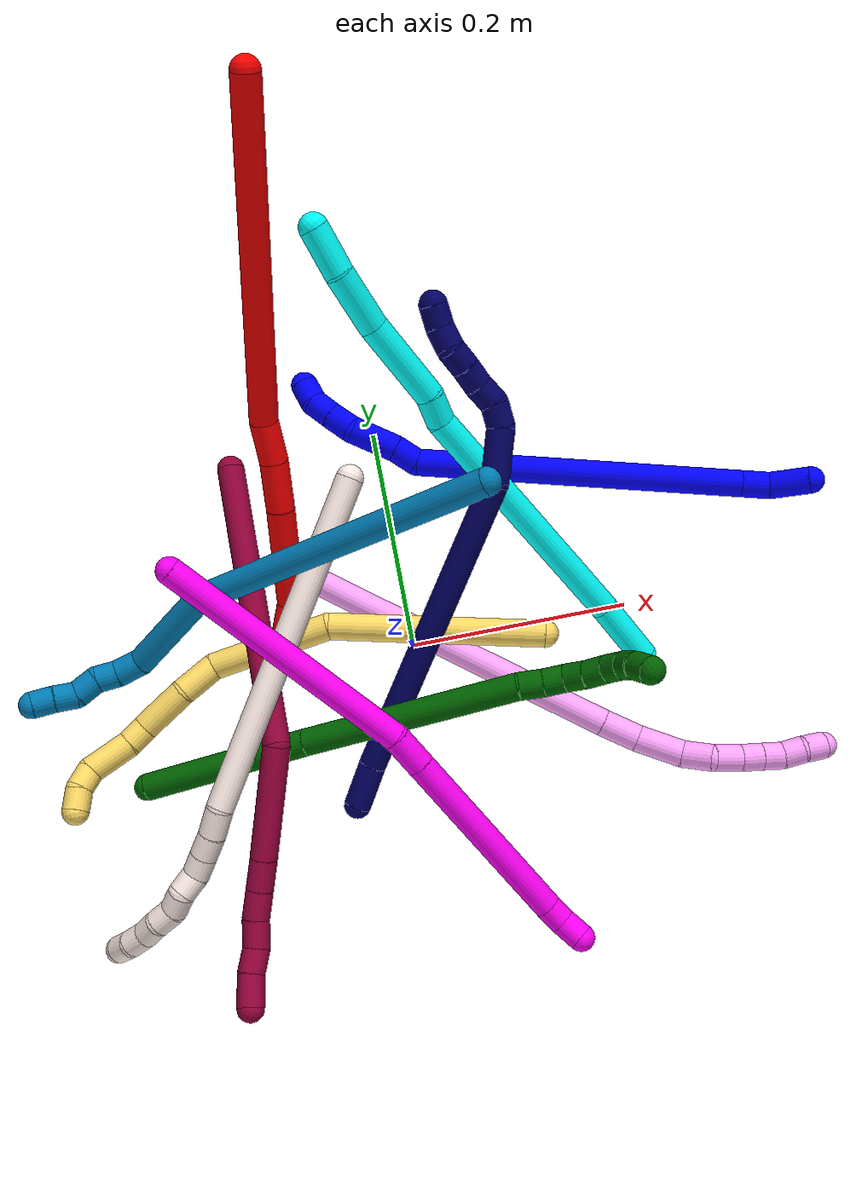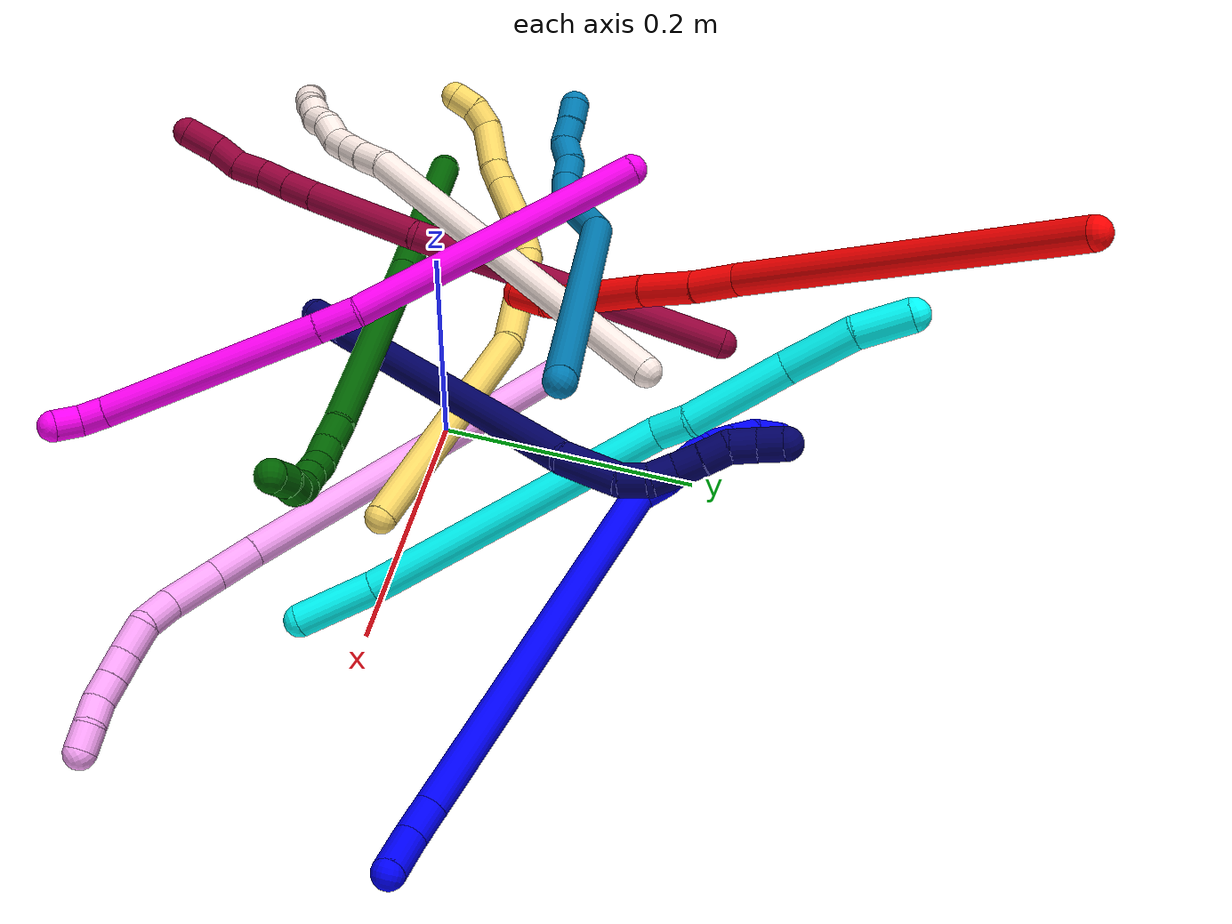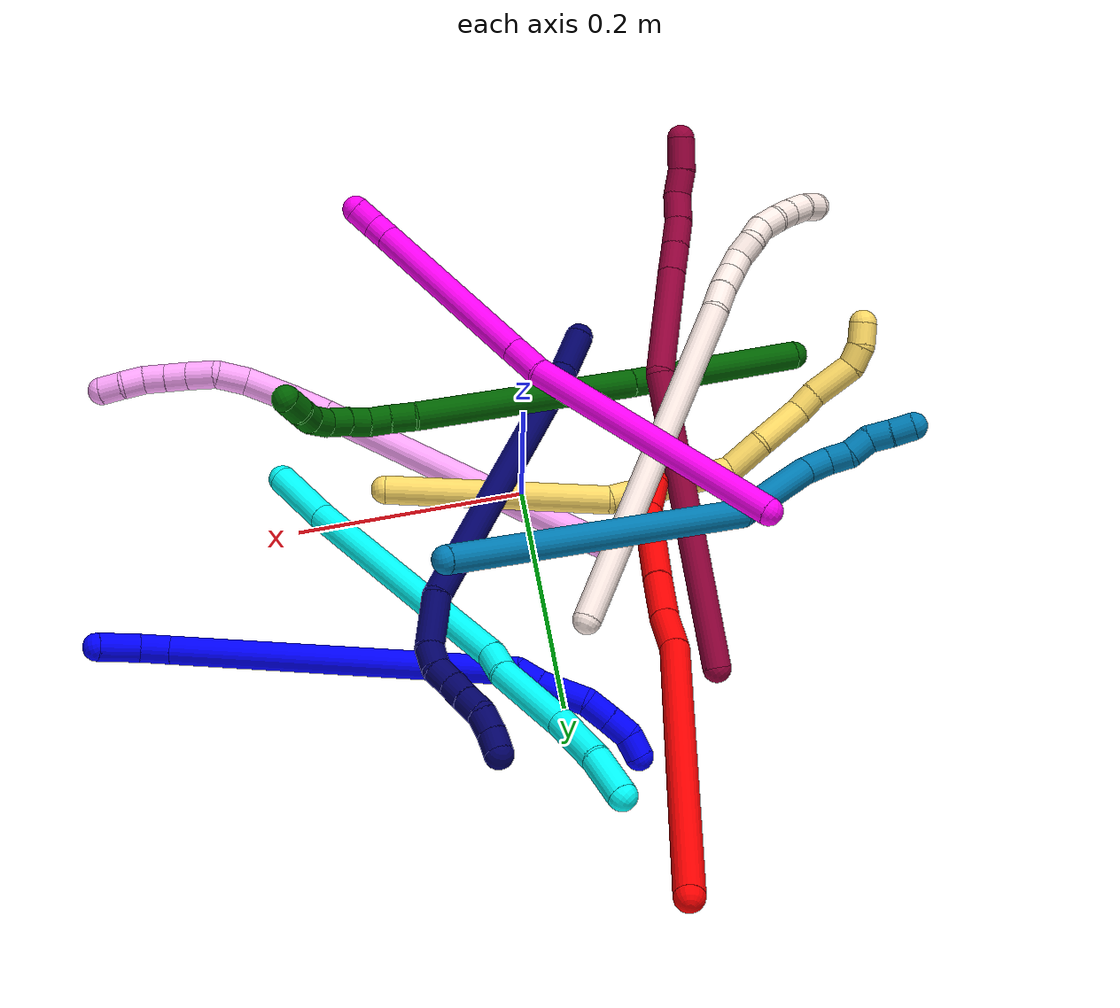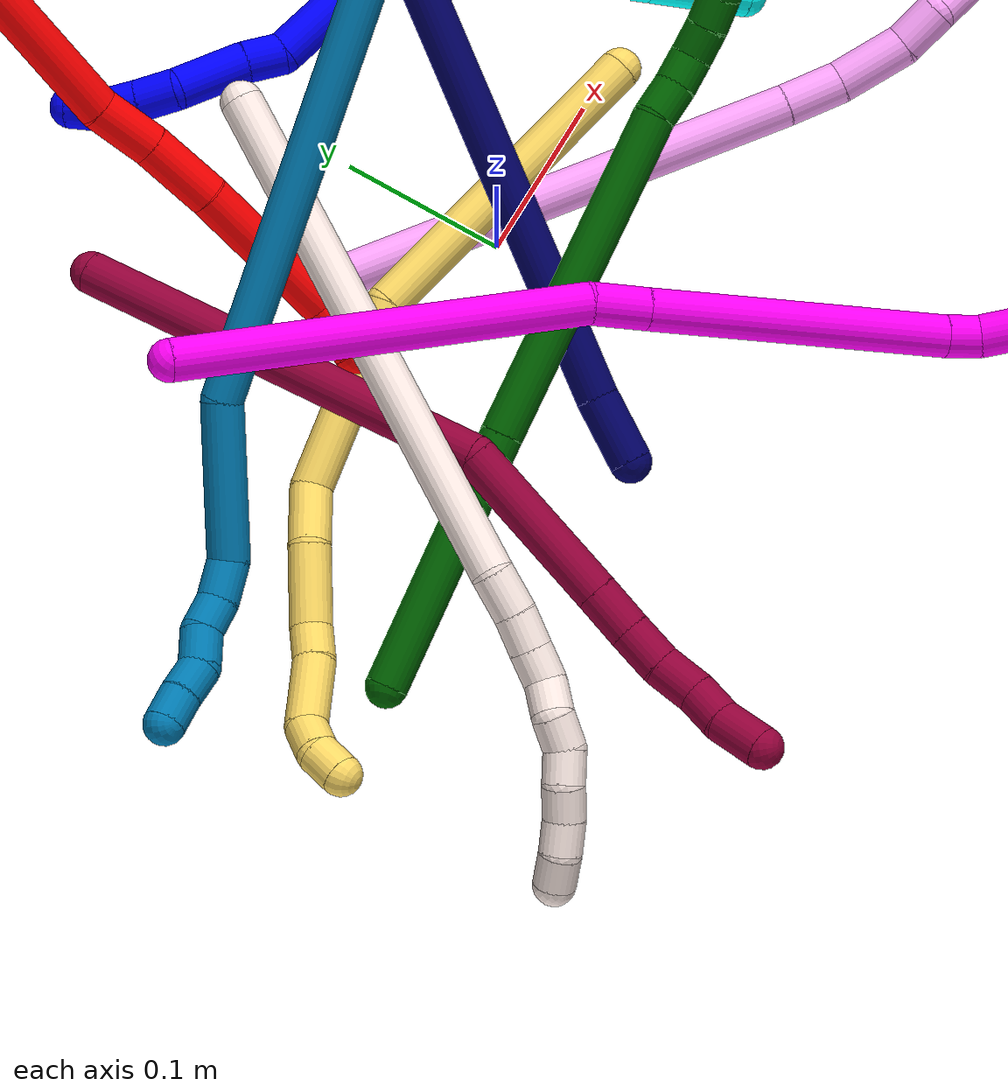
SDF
<sdf version="1.7">
 <world name="default">
  <plugin name="TubeGeneratorPlugin" filename="libtube_generator_plugin.so"/>
  <model name="photoneo_s_sensor">
   <static>1</static>
   <pose>0 0 2 1.57079 1.57079 3.14159</pose>
   <link name="link">
    <inertial><mass>0.1</mass></inertial>
    <sensor name="sensor" type="depth">
     <update_rate>30</update_rate>
     <camera>
      <horizontal_fov>1.22</horizontal_fov>
      <image><width>1920</width><height>1200</height><format>B8G8R8</format></image>
      <clip><near>0.1</near><far>4</far></clip>
      <depth_camera><output>points</output></depth_camera>
     </camera>
     <plugin name="camera_plugin" filename="libgazebo_ros_depth_camera.so">
      <baseline>0.2</baseline>
      <alwaysOn>1</alwaysOn>
      <updateRate>0.0</updateRate>
      <cameraName>camera_ir</cameraName>
      <imageTopicName>/camera/color/image_raw</imageTopicName>
      <cameraInfoTopicName>/camera/color/camera_info</cameraInfoTopicName>
      <depthImageTopicName>/camera/depth/image_raw</depthImageTopicName>
      <depthImageCameraInfoTopicName>/camera/depth/camera_info</depthImageCameraInfoTopicName>
      <pointCloudTopicName>/camera/depth/points</pointCloudTopicName>
      <frameName>fr_optical</frameName>
      <pointCloudCutoff>0.1</pointCloudCutoff>
      <pointCloudCutoffMax>2.0</pointCloudCutoffMax>
      <distortionK1>0</distortionK1>
      <distortionK2>0</distortionK2>
      <distortionK3>0</distortionK3>
      <distortionT1>0</distortionT1>
      <distortionT2>0</distortionT2>
      <CxPrime>0</CxPrime>
      <Cx>0</Cx>
      <Cy>0</Cy>
      <focalLength>0</focalLength>
      <hackBaseline>0</hackBaseline>
     </plugin>
    </sensor>
   </link>
  </model>
  <gravity>0 0 -9.8</gravity>
  <magnetic_field>6e-06 2.3e-05 -4.2e-05</magnetic_field>
  <atmosphere type="adiabatic"/>
  <physics name="default_physics" default="0" type="ode">
   <max_step_size>0.003</max_step_size>
   <real_time_factor>1</real_time_factor>
   <real_time_update_rate>1000</real_time_update_rate>
   <max_contacts>10000</max_contacts>
   <ode>
    <solver>
     <type>quick</type>
     <iters>100</iters>
     <sor>1.3</sor>
     <use_dynamic_moi_rescaling>0</use_dynamic_moi_rescaling>
    </solver>
    <constraints>
     <contact_max_correcting_vel>0</contact_max_correcting_vel>
     <contact_surface_layer>0.001</contact_surface_layer>
     <cfm>0</cfm>
     <erp>0.2</erp>
    </constraints>
   </ode>
  </physics>
  <scene><ambient>0.4 0.4 0.4 1</ambient><background>0.7 0.7 0.7 1</background><shadows>0</shadows></scene>
  <audio><device>default</device></audio>
  <spherical_coordinates>
   <surface_model>EARTH_WGS84</surface_model>
   <latitude_deg>0</latitude_deg>
   <longitude_deg>0</longitude_deg>
   <elevation>0</elevation>
   <heading_deg>0</heading_deg>
  </spherical_coordinates>
  <model name="bin">
   <static>1</static>
   <link name="bottom">
    <collision name="collision-bottom">
     <pose>0 0 -0.01 0 -0 0</pose>
     <geometry><box><size>0.8 0.6 0.02</size></box></geometry>
     <surface>
      <friction><ode><mu>100</mu><mu2>100</mu2></ode></friction>
      <contact><collide_bitmask>65535</collide_bitmask></contact>
     </surface>
    </collision>
   </link>
   <link name="west_wall">
    <collision name="collision-west_wall">
     <pose>-0.41 0 0.1 0 -0 0</pose>
     <geometry><box><size>0.02 0.6 0.2</size></box></geometry>
     <surface>
      <friction><ode><mu>100</mu><mu2>100</mu2></ode></friction>
      <contact><collide_bitmask>65535</collide_bitmask></contact>
     </surface>
    </collision>
   </link>
   <link name="east_wall">
    <collision name="collision-east_wall">
     <pose>0.41 0 0.1 0 -0 0</pose>
     <geometry><box><size>0.02 0.6 0.2</size></box></geometry>
     <surface>
      <friction><ode><mu>100</mu><mu2>100</mu2></ode></friction>
      <contact><collide_bitmask>65535</collide_bitmask></contact>
     </surface>
    </collision>
   </link>
   <link name="south_wall">
    <collision name="collision-south_wall">
     <pose>0 -0.31 0.1 0 -0 0</pose>
     <geometry><box><size>0.8 0.02 0.2</size></box></geometry>
     <surface>
      <friction><ode><mu>100</mu><mu2>100</mu2></ode></friction>
      <contact><collide_bitmask>65535</collide_bitmask></contact>
     </surface>
    </collision>
   </link>
   <link name="north_wall">
    <collision name="collision-north_wall">
     <pose>0 0.31 0.1 0 -0 0</pose>
     <geometry><box><size>0.8 0.02 0.2</size></box></geometry>
     <surface>
      <friction><ode><mu>100</mu><mu2>100</mu2></ode></friction>
      <contact><collide_bitmask>65535</collide_bitmask></contact>
     </surface>
    </collision>
   </link>
  </model>
  <model name="1">
   <static>0</static>
   <link name="1">
    <collision name="collision-cylinder-e_1_1_4">
     <pose>-0.01138 0.009706 -0.011918 -2.45812 -0.637345 1.49565</pose>
     <geometry><cylinder><radius>0.0125</radius><length>0.038249</length></cylinder></geometry>
     <surface>
      <friction><ode><mu>1.16</mu><mu2>1.16</mu2><slip1>0</slip1><slip2>0</slip2></ode></friction>
      <contact><ode><kp>1e+06</kp><kd>1</kd><max_vel>0</max_vel><min_depth>0.001</min_depth></ode></contact>
     </surface>
    </collision>
    <visual name="visual-cylinder-e_1_1_4">
     <pose>-0.01138 0.009706 -0.011918 -2.45812 -0.637345 1.49565</pose>
     <geometry><cylinder><radius>0.0125</radius><length>0.038249</length></cylinder></geometry>
     <material><ambient>0 0 1 1</ambient></material>
    </visual>
    <collision name="collision-cylinder-e_2_4_5">
     <pose>-0.029485 0.021566 -0.035536 -2.95954 -0.514452 2.47361</pose>
     <geometry><cylinder><radius>0.0125</radius><length>0.027332</length></cylinder></geometry>
     <surface>
      <friction><ode><mu>1.16</mu><mu2>1.16</mu2><slip1>0</slip1><slip2>0</slip2></ode></friction>
      <contact><ode><kp>1e+06</kp><kd>1</kd><max_vel>0</max_vel><min_depth>0.001</min_depth></ode></contact>
     </surface>
    </collision>
    <visual name="visual-cylinder-e_2_4_5">
     <pose>-0.029485 0.021566 -0.035536 -2.95954 -0.514452 2.47361</pose>
     <geometry><cylinder><radius>0.0125</radius><length>0.027332</length></cylinder></geometry>
     <material><ambient>0 0 1 1</ambient></material>
    </visual>
    <collision name="collision-cylinder-e_3_5_6">
     <pose>-0.110078 0.04758 -0.176394 -2.95891 -0.512318 2.46875</pose>
     <geometry><cylinder><radius>0.0125</radius><length>0.301381</length></cylinder></geometry>
     <surface>
      <friction><ode><mu>1.16</mu><mu2>1.16</mu2><slip1>0</slip1><slip2>0</slip2></ode></friction>
      <contact><ode><kp>1e+06</kp><kd>1</kd><max_vel>0</max_vel><min_depth>0.001</min_depth></ode></contact>
     </surface>
    </collision>
    <visual name="visual-cylinder-e_3_5_6">
     <pose>-0.110078 0.04758 -0.176394 -2.95891 -0.512318 2.46875</pose>
     <geometry><cylinder><radius>0.0125</radius><length>0.301381</length></cylinder></geometry>
     <material><ambient>0 0 1 1</ambient></material>
    </visual>
    <collision name="collision-cylinder-e_4_6_7">
     <pose>-0.191898 0.068237 -0.313573 2.7616 -0.744118 -2.22581</pose>
     <geometry><cylinder><radius>0.0125</radius><length>0.023479</length></cylinder></geometry>
     <surface>
      <friction><ode><mu>1.16</mu><mu2>1.16</mu2><slip1>0</slip1><slip2>0</slip2></ode></friction>
      <contact><ode><kp>1e+06</kp><kd>1</kd><max_vel>0</max_vel><min_depth>0.001</min_depth></ode></contact>
     </surface>
    </collision>
    <visual name="visual-cylinder-e_4_6_7">
     <pose>-0.191898 0.068237 -0.313573 2.7616 -0.744118 -2.22581</pose>
     <geometry><cylinder><radius>0.0125</radius><length>0.023479</length></cylinder></geometry>
     <material><ambient>0 0 1 1</ambient></material>
    </visual>
    <collision name="collision-cylinder-e_5_7_8">
     <pose>-0.212707 0.06141 -0.338722 2.9331 -0.633422 -2.52358</pose>
     <geometry><cylinder><radius>0.0125</radius><length>0.043443</length></cylinder></geometry>
     <surface>
      <friction><ode><mu>1.16</mu><mu2>1.16</mu2><slip1>0</slip1><slip2>0</slip2></ode></friction>
      <contact><ode><kp>1e+06</kp><kd>1</kd><max_vel>0</max_vel><min_depth>0.001</min_depth></ode></contact>
     </surface>
    </collision>
    <visual name="visual-cylinder-e_5_7_8">
     <pose>-0.212707 0.06141 -0.338722 2.9331 -0.633422 -2.52358</pose>
     <geometry><cylinder><radius>0.0125</radius><length>0.043443</length></cylinder></geometry>
     <material><ambient>0 0 1 1</ambient></material>
    </visual>
    <collision name="collision-cylinder-e_6_8_9">
     <pose>-0.235827 0.056534 -0.361471 2.92244 -1.05951 -2.77018</pose>
     <geometry><cylinder><radius>0.0125</radius><length>0.023538</length></cylinder></geometry>
     <surface>
      <friction><ode><mu>1.16</mu><mu2>1.16</mu2><slip1>0</slip1><slip2>0</slip2></ode></friction>
      <contact><ode><kp>1e+06</kp><kd>1</kd><max_vel>0</max_vel><min_depth>0.001</min_depth></ode></contact>
     </surface>
    </collision>
    <visual name="visual-cylinder-e_6_8_9">
     <pose>-0.235827 0.056534 -0.361471 2.92244 -1.05951 -2.77018</pose>
     <geometry><cylinder><radius>0.0125</radius><length>0.023538</length></cylinder></geometry>
     <material><ambient>0 0 1 1</ambient></material>
    </visual>
    <collision name="collision-cylinder-e_7_9_10">
     <pose>-0.255804 0.053609 -0.3723 2.83063 -1.05792 -2.61759</pose>
     <geometry><cylinder><radius>0.0125</radius><length>0.022294</length></cylinder></geometry>
     <surface>
      <friction><ode><mu>1.16</mu><mu2>1.16</mu2><slip1>0</slip1><slip2>0</slip2></ode></friction>
      <contact><ode><kp>1e+06</kp><kd>1</kd><max_vel>0</max_vel><min_depth>0.001</min_depth></ode></contact>
     </surface>
    </collision>
    <visual name="visual-cylinder-e_7_9_10">
     <pose>-0.255804 0.053609 -0.3723 2.83063 -1.05792 -2.61759</pose>
     <geometry><cylinder><radius>0.0125</radius><length>0.022294</length></cylinder></geometry>
     <material><ambient>0 0 1 1</ambient></material>
    </visual>
    <collision name="collision-cylinder-e_8_10_2">
     <pose>-0.274937 0.048398 -0.378775 1.91491 -1.19129 -1.53296</pose>
     <geometry><cylinder><radius>0.0125</radius><length>0.020283</length></cylinder></geometry>
     <surface>
      <friction><ode><mu>1.16</mu><mu2>1.16</mu2><slip1>0</slip1><slip2>0</slip2></ode></friction>
      <contact><ode><kp>1e+06</kp><kd>1</kd><max_vel>0</max_vel><min_depth>0.001</min_depth></ode></contact>
     </surface>
    </collision>
    <visual name="visual-cylinder-e_8_10_2">
     <pose>-0.274937 0.048398 -0.378775 1.91491 -1.19129 -1.53296</pose>
     <geometry><cylinder><radius>0.0125</radius><length>0.020283</length></cylinder></geometry>
     <material><ambient>0 0 1 1</ambient></material>
    </visual>
    <collision name="collision-sphere-2">
     <pose>-0.284357 0.044861 -0.380042 0 -0 0</pose>
     <geometry><sphere><radius>0.0125</radius></sphere></geometry>
     <surface>
      <friction><ode><mu>1.16</mu><mu2>1.16</mu2><slip1>0</slip1><slip2>0</slip2></ode></friction>
      <contact><ode><kp>1e+06</kp><kd>1</kd><max_vel>0</max_vel><min_depth>0.001</min_depth></ode></contact>
     </surface>
    </collision>
    <visual name="visual-sphere-2">
     <pose>-0.284357 0.044861 -0.380042 0 -0 0</pose>
     <geometry><sphere><radius>0.0125</radius></sphere></geometry>
     <material><ambient>0 0 1 1</ambient></material>
    </visual>
    <collision name="collision-sphere-10">
     <pose>-0.265517 0.051935 -0.377507 0 -0 0</pose>
     <geometry><sphere><radius>0.0125</radius></sphere></geometry>
     <surface>
      <friction><ode><mu>1.16</mu><mu2>1.16</mu2><slip1>0</slip1><slip2>0</slip2></ode></friction>
      <contact><ode><kp>1e+06</kp><kd>1</kd><max_vel>0</max_vel><min_depth>0.001</min_depth></ode></contact>
     </surface>
    </collision>
    <visual name="visual-sphere-10">
     <pose>-0.265517 0.051935 -0.377507 0 -0 0</pose>
     <geometry><sphere><radius>0.0125</radius></sphere></geometry>
     <material><ambient>0 0 1 1</ambient></material>
    </visual>
    <collision name="collision-sphere-9">
     <pose>-0.246091 0.055282 -0.367092 0 -0 0</pose>
     <geometry><sphere><radius>0.0125</radius></sphere></geometry>
     <surface>
      <friction><ode><mu>1.16</mu><mu2>1.16</mu2><slip1>0</slip1><slip2>0</slip2></ode></friction>
      <contact><ode><kp>1e+06</kp><kd>1</kd><max_vel>0</max_vel><min_depth>0.001</min_depth></ode></contact>
     </surface>
    </collision>
    <visual name="visual-sphere-9">
     <pose>-0.246091 0.055282 -0.367092 0 -0 0</pose>
     <geometry><sphere><radius>0.0125</radius></sphere></geometry>
     <material><ambient>0 0 1 1</ambient></material>
    </visual>
    <collision name="collision-sphere-4">
     <pose>-0.022761 0.019412 -0.023835 0 -0 0</pose>
     <geometry><sphere><radius>0.0125</radius></sphere></geometry>
     <surface>
      <friction><ode><mu>1.16</mu><mu2>1.16</mu2><slip1>0</slip1><slip2>0</slip2></ode></friction>
      <contact><ode><kp>1e+06</kp><kd>1</kd><max_vel>0</max_vel><min_depth>0.001</min_depth></ode></contact>
     </surface>
    </collision>
    <visual name="visual-sphere-4">
     <pose>-0.022761 0.019412 -0.023835 0 -0 0</pose>
     <geometry><sphere><radius>0.0125</radius></sphere></geometry>
     <material><ambient>0 0 1 1</ambient></material>
    </visual>
    <collision name="collision-sphere-1">
     <geometry><sphere><radius>0.0125</radius></sphere></geometry>
     <surface>
      <friction><ode><mu>1.16</mu><mu2>1.16</mu2><slip1>0</slip1><slip2>0</slip2></ode></friction>
      <contact><ode><kp>1e+06</kp><kd>1</kd><max_vel>0</max_vel><min_depth>0.001</min_depth></ode></contact>
     </surface>
    </collision>
    <visual name="visual-sphere-1">
     <geometry><sphere><radius>0.0125</radius></sphere></geometry>
     <material><ambient>0 0 1 1</ambient></material>
    </visual>
    <collision name="collision-sphere-8">
     <pose>-0.225564 0.057786 -0.355851 0 -0 0</pose>
     <geometry><sphere><radius>0.0125</radius></sphere></geometry>
     <surface>
      <friction><ode><mu>1.16</mu><mu2>1.16</mu2><slip1>0</slip1><slip2>0</slip2></ode></friction>
      <contact><ode><kp>1e+06</kp><kd>1</kd><max_vel>0</max_vel><min_depth>0.001</min_depth></ode></contact>
     </surface>
    </collision>
    <visual name="visual-sphere-8">
     <pose>-0.225564 0.057786 -0.355851 0 -0 0</pose>
     <geometry><sphere><radius>0.0125</radius></sphere></geometry>
     <material><ambient>0 0 1 1</ambient></material>
    </visual>
    <collision name="collision-sphere-5">
     <pose>-0.03621 0.02372 -0.047236 0 -0 0</pose>
     <geometry><sphere><radius>0.0125</radius></sphere></geometry>
     <surface>
      <friction><ode><mu>1.16</mu><mu2>1.16</mu2><slip1>0</slip1><slip2>0</slip2></ode></friction>
      <contact><ode><kp>1e+06</kp><kd>1</kd><max_vel>0</max_vel><min_depth>0.001</min_depth></ode></contact>
     </surface>
    </collision>
    <visual name="visual-sphere-5">
     <pose>-0.03621 0.02372 -0.047236 0 -0 0</pose>
     <geometry><sphere><radius>0.0125</radius></sphere></geometry>
     <material><ambient>0 0 1 1</ambient></material>
    </visual>
    <collision name="collision-sphere-6">
     <pose>-0.183946 0.071441 -0.305552 0 -0 0</pose>
     <geometry><sphere><radius>0.0125</radius></sphere></geometry>
     <surface>
      <friction><ode><mu>1.16</mu><mu2>1.16</mu2><slip1>0</slip1><slip2>0</slip2></ode></friction>
      <contact><ode><kp>1e+06</kp><kd>1</kd><max_vel>0</max_vel><min_depth>0.001</min_depth></ode></contact>
     </surface>
    </collision>
    <visual name="visual-sphere-6">
     <pose>-0.183946 0.071441 -0.305552 0 -0 0</pose>
     <geometry><sphere><radius>0.0125</radius></sphere></geometry>
     <material><ambient>0 0 1 1</ambient></material>
    </visual>
    <collision name="collision-sphere-7">
     <pose>-0.199849 0.065034 -0.321594 0 -0 0</pose>
     <geometry><sphere><radius>0.0125</radius></sphere></geometry>
     <surface>
      <friction><ode><mu>1.16</mu><mu2>1.16</mu2><slip1>0</slip1><slip2>0</slip2></ode></friction>
      <contact><ode><kp>1e+06</kp><kd>1</kd><max_vel>0</max_vel><min_depth>0.001</min_depth></ode></contact>
     </surface>
    </collision>
    <visual name="visual-sphere-7">
     <pose>-0.199849 0.065034 -0.321594 0 -0 0</pose>
     <geometry><sphere><radius>0.0125</radius></sphere></geometry>
     <material><ambient>0 0 1 1</ambient></material>
    </visual>
    <inertial>
     <pose>-0.129987 0.046156 -0.202316 0 -0 0</pose>
     <mass>0.5</mass>
     <inertia>
      <ixx>-0.000349</ixx>
      <ixy>0</ixy>
      <ixz>0</ixz>
      <iyy>0.003158</iyy>
      <iyz>0</iyz>
      <izz>0.000747</izz>
     </inertia>
    </inertial>
   </link>
   <pose>0.3883 0.079809 0.026536 -2.23077 -0.650022 -1.13955</pose>
  </model>
  <model name="2">
   <static>0</static>
   <link name="2">
    <collision name="collision-cylinder-e_1_1_4">
     <pose>-0.00029 0.008816 -0.146254 -3.08139 -0.001978 0.065666</pose>
     <geometry><cylinder><radius>0.0125</radius><length>0.293039</length></cylinder></geometry>
     <surface>
      <friction><ode><mu>1.16</mu><mu2>1.16</mu2><slip1>0</slip1><slip2>0</slip2></ode></friction>
      <contact><ode><kp>1e+06</kp><kd>1</kd><max_vel>0</max_vel><min_depth>0.001</min_depth></ode></contact>
     </surface>
    </collision>
    <visual name="visual-cylinder-e_1_1_4">
     <pose>-0.00029 0.008816 -0.146254 -3.08139 -0.001978 0.065666</pose>
     <geometry><cylinder><radius>0.0125</radius><length>0.293039</length></cylinder></geometry>
     <material><ambient>1 0 0 1</ambient></material>
    </visual>
    <collision name="collision-cylinder-e_2_4_5">
     <pose>0.002159 0.015623 -0.310561 3.03079 0.149621 1.86755</pose>
     <geometry><cylinder><radius>0.0125</radius><length>0.036741</length></cylinder></geometry>
     <surface>
      <friction><ode><mu>1.16</mu><mu2>1.16</mu2><slip1>0</slip1><slip2>0</slip2></ode></friction>
      <contact><ode><kp>1e+06</kp><kd>1</kd><max_vel>0</max_vel><min_depth>0.001</min_depth></ode></contact>
     </surface>
    </collision>
    <visual name="visual-cylinder-e_2_4_5">
     <pose>0.002159 0.015623 -0.310561 3.03079 0.149621 1.86755</pose>
     <geometry><cylinder><radius>0.0125</radius><length>0.036741</length></cylinder></geometry>
     <material><ambient>1 0 0 1</ambient></material>
    </visual>
    <collision name="collision-cylinder-e_3_5_6">
     <pose>0.005888 0.011326 -0.350513 3.03747 0.044981 0.815051</pose>
     <geometry><cylinder><radius>0.0125</radius><length>0.04408</length></cylinder></geometry>
     <surface>
      <friction><ode><mu>1.16</mu><mu2>1.16</mu2><slip1>0</slip1><slip2>0</slip2></ode></friction>
      <contact><ode><kp>1e+06</kp><kd>1</kd><max_vel>0</max_vel><min_depth>0.001</min_depth></ode></contact>
     </surface>
    </collision>
    <visual name="visual-cylinder-e_3_5_6">
     <pose>0.005888 0.011326 -0.350513 3.03747 0.044981 0.815051</pose>
     <geometry><cylinder><radius>0.0125</radius><length>0.04408</length></cylinder></geometry>
     <material><ambient>1 0 0 1</ambient></material>
    </visual>
    <collision name="collision-cylinder-e_4_6_7">
     <pose>0.00878 0.008294 -0.419253 3.1257 0.040558 2.39489</pose>
     <geometry><cylinder><radius>0.0125</radius><length>0.093772</length></cylinder></geometry>
     <surface>
      <friction><ode><mu>1.16</mu><mu2>1.16</mu2><slip1>0</slip1><slip2>0</slip2></ode></friction>
      <contact><ode><kp>1e+06</kp><kd>1</kd><max_vel>0</max_vel><min_depth>0.001</min_depth></ode></contact>
     </surface>
    </collision>
    <visual name="visual-cylinder-e_4_6_7">
     <pose>0.00878 0.008294 -0.419253 3.1257 0.040558 2.39489</pose>
     <geometry><cylinder><radius>0.0125</radius><length>0.093772</length></cylinder></geometry>
     <material><ambient>1 0 0 1</ambient></material>
    </visual>
    <collision name="collision-cylinder-e_5_7_2">
     <pose>0.006238 0.005461 -0.481516 3.00702 -0.278117 -2.24415</pose>
     <geometry><cylinder><radius>0.0125</radius><length>0.032368</length></cylinder></geometry>
     <surface>
      <friction><ode><mu>1.16</mu><mu2>1.16</mu2><slip1>0</slip1><slip2>0</slip2></ode></friction>
      <contact><ode><kp>1e+06</kp><kd>1</kd><max_vel>0</max_vel><min_depth>0.001</min_depth></ode></contact>
     </surface>
    </collision>
    <visual name="visual-cylinder-e_5_7_2">
     <pose>0.006238 0.005461 -0.481516 3.00702 -0.278117 -2.24415</pose>
     <geometry><cylinder><radius>0.0125</radius><length>0.032368</length></cylinder></geometry>
     <material><ambient>1 0 0 1</ambient></material>
    </visual>
    <collision name="collision-sphere-2">
     <pose>0.001795 0.003373 -0.496938 0 -0 0</pose>
     <geometry><sphere><radius>0.0125</radius></sphere></geometry>
     <surface>
      <friction><ode><mu>1.16</mu><mu2>1.16</mu2><slip1>0</slip1><slip2>0</slip2></ode></friction>
      <contact><ode><kp>1e+06</kp><kd>1</kd><max_vel>0</max_vel><min_depth>0.001</min_depth></ode></contact>
     </surface>
    </collision>
    <visual name="visual-sphere-2">
     <pose>0.001795 0.003373 -0.496938 0 -0 0</pose>
     <geometry><sphere><radius>0.0125</radius></sphere></geometry>
     <material><ambient>1 0 0 1</ambient></material>
    </visual>
    <collision name="collision-sphere-7">
     <pose>0.010681 0.007549 -0.466095 0 -0 0</pose>
     <geometry><sphere><radius>0.0125</radius></sphere></geometry>
     <surface>
      <friction><ode><mu>1.16</mu><mu2>1.16</mu2><slip1>0</slip1><slip2>0</slip2></ode></friction>
      <contact><ode><kp>1e+06</kp><kd>1</kd><max_vel>0</max_vel><min_depth>0.001</min_depth></ode></contact>
     </surface>
    </collision>
    <visual name="visual-sphere-7">
     <pose>0.010681 0.007549 -0.466095 0 -0 0</pose>
     <geometry><sphere><radius>0.0125</radius></sphere></geometry>
     <material><ambient>1 0 0 1</ambient></material>
    </visual>
    <collision name="collision-sphere-6">
     <pose>0.006879 0.009038 -0.372412 0 -0 0</pose>
     <geometry><sphere><radius>0.0125</radius></sphere></geometry>
     <surface>
      <friction><ode><mu>1.16</mu><mu2>1.16</mu2><slip1>0</slip1><slip2>0</slip2></ode></friction>
      <contact><ode><kp>1e+06</kp><kd>1</kd><max_vel>0</max_vel><min_depth>0.001</min_depth></ode></contact>
     </surface>
    </collision>
    <visual name="visual-sphere-6">
     <pose>0.006879 0.009038 -0.372412 0 -0 0</pose>
     <geometry><sphere><radius>0.0125</radius></sphere></geometry>
     <material><ambient>1 0 0 1</ambient></material>
    </visual>
    <collision name="collision-sphere-5">
     <pose>0.004897 0.013615 -0.328615 0 -0 0</pose>
     <geometry><sphere><radius>0.0125</radius></sphere></geometry>
     <surface>
      <friction><ode><mu>1.16</mu><mu2>1.16</mu2><slip1>0</slip1><slip2>0</slip2></ode></friction>
      <contact><ode><kp>1e+06</kp><kd>1</kd><max_vel>0</max_vel><min_depth>0.001</min_depth></ode></contact>
     </surface>
    </collision>
    <visual name="visual-sphere-5">
     <pose>0.004897 0.013615 -0.328615 0 -0 0</pose>
     <geometry><sphere><radius>0.0125</radius></sphere></geometry>
     <material><ambient>1 0 0 1</ambient></material>
    </visual>
    <collision name="collision-sphere-1">
     <geometry><sphere><radius>0.0125</radius></sphere></geometry>
     <surface>
      <friction><ode><mu>1.16</mu><mu2>1.16</mu2><slip1>0</slip1><slip2>0</slip2></ode></friction>
      <contact><ode><kp>1e+06</kp><kd>1</kd><max_vel>0</max_vel><min_depth>0.001</min_depth></ode></contact>
     </surface>
    </collision>
    <visual name="visual-sphere-1">
     <geometry><sphere><radius>0.0125</radius></sphere></geometry>
     <material><ambient>1 0 0 1</ambient></material>
    </visual>
    <collision name="collision-sphere-4">
     <pose>-0.00058 0.017632 -0.292507 0 -0 0</pose>
     <geometry><sphere><radius>0.0125</radius></sphere></geometry>
     <surface>
      <friction><ode><mu>1.16</mu><mu2>1.16</mu2><slip1>0</slip1><slip2>0</slip2></ode></friction>
      <contact><ode><kp>1e+06</kp><kd>1</kd><max_vel>0</max_vel><min_depth>0.001</min_depth></ode></contact>
     </surface>
    </collision>
    <visual name="visual-sphere-4">
     <pose>-0.00058 0.017632 -0.292507 0 -0 0</pose>
     <geometry><sphere><radius>0.0125</radius></sphere></geometry>
     <material><ambient>1 0 0 1</ambient></material>
    </visual>
    <inertial>
     <pose>0.002558 0.009222 -0.249238 0 -0 0</pose>
     <mass>0.5</mass>
     <inertia>
      <ixx>0.002249</ixx>
      <ixy>0</ixy>
      <ixz>0</ixz>
      <iyy>-0.001852</iyy>
      <iyz>0</iyz>
      <izz>-0.000161</izz>
     </inertia>
    </inertial>
   </link>
   <pose>-0.040679 0.442279 0.316303 -0.988297 0.279137 0.007842</pose>
  </model>
  <model name="3">
   <static>0</static>
   <link name="3">
    <collision name="collision-cylinder-e_1_1_4">
     <pose>-0.006073 0.006809 0.029231 -0.228858 -0.199635 0.02302</pose>
     <geometry><cylinder><radius>0.0125</radius><length>0.061244</length></cylinder></geometry>
     <surface>
      <friction><ode><mu>1.16</mu><mu2>1.16</mu2><slip1>0</slip1><slip2>0</slip2></ode></friction>
      <contact><ode><kp>1e+06</kp><kd>1</kd><max_vel>0</max_vel><min_depth>0.001</min_depth></ode></contact>
     </surface>
    </collision>
    <visual name="visual-cylinder-e_1_1_4">
     <pose>-0.006073 0.006809 0.029231 -0.228858 -0.199635 0.02302</pose>
     <geometry><cylinder><radius>0.0125</radius><length>0.061244</length></cylinder></geometry>
     <material><ambient>0.003922 1 0.996078 1</ambient></material>
    </visual>
    <collision name="collision-cylinder-e_2_4_5">
     <pose>-0.034601 0.049516 0.169553 -0.312548 -0.190024 0.030028</pose>
     <geometry><cylinder><radius>0.0125</radius><length>0.237773</length></cylinder></geometry>
     <surface>
      <friction><ode><mu>1.16</mu><mu2>1.16</mu2><slip1>0</slip1><slip2>0</slip2></ode></friction>
      <contact><ode><kp>1e+06</kp><kd>1</kd><max_vel>0</max_vel><min_depth>0.001</min_depth></ode></contact>
     </surface>
    </collision>
    <visual name="visual-cylinder-e_2_4_5">
     <pose>-0.034601 0.049516 0.169553 -0.312548 -0.190024 0.030028</pose>
     <geometry><cylinder><radius>0.0125</radius><length>0.237773</length></cylinder></geometry>
     <material><ambient>0.003922 1 0.996078 1</ambient></material>
    </visual>
    <collision name="collision-cylinder-e_3_5_6">
     <pose>-0.063509 0.089551 0.291637 -0.3599 -0.502304 0.093281</pose>
     <geometry><cylinder><radius>0.0125</radius><length>0.026804</length></cylinder></geometry>
     <surface>
      <friction><ode><mu>1.16</mu><mu2>1.16</mu2><slip1>0</slip1><slip2>0</slip2></ode></friction>
      <contact><ode><kp>1e+06</kp><kd>1</kd><max_vel>0</max_vel><min_depth>0.001</min_depth></ode></contact>
     </surface>
    </collision>
    <visual name="visual-cylinder-e_3_5_6">
     <pose>-0.063509 0.089551 0.291637 -0.3599 -0.502304 0.093281</pose>
     <geometry><cylinder><radius>0.0125</radius><length>0.026804</length></cylinder></geometry>
     <material><ambient>0.003922 1 0.996078 1</ambient></material>
    </visual>
    <collision name="collision-cylinder-e_4_6_7">
     <pose>-0.079013 0.106702 0.338456 -0.34846 -0.233177 0.041224</pose>
     <geometry><cylinder><radius>0.0125</radius><length>0.078351</length></cylinder></geometry>
     <surface>
      <friction><ode><mu>1.16</mu><mu2>1.16</mu2><slip1>0</slip1><slip2>0</slip2></ode></friction>
      <contact><ode><kp>1e+06</kp><kd>1</kd><max_vel>0</max_vel><min_depth>0.001</min_depth></ode></contact>
     </surface>
    </collision>
    <visual name="visual-cylinder-e_4_6_7">
     <pose>-0.079013 0.106702 0.338456 -0.34846 -0.233177 0.041224</pose>
     <geometry><cylinder><radius>0.0125</radius><length>0.078351</length></cylinder></geometry>
     <material><ambient>0.003922 1 0.996078 1</ambient></material>
    </visual>
    <collision name="collision-cylinder-e_5_7_8">
     <pose>-0.09738 0.12953 0.397661 -0.397392 -0.352022 0.071591</pose>
     <geometry><cylinder><radius>0.0125</radius><length>0.054027</length></cylinder></geometry>
     <surface>
      <friction><ode><mu>1.16</mu><mu2>1.16</mu2><slip1>0</slip1><slip2>0</slip2></ode></friction>
      <contact><ode><kp>1e+06</kp><kd>1</kd><max_vel>0</max_vel><min_depth>0.001</min_depth></ode></contact>
     </surface>
    </collision>
    <visual name="visual-cylinder-e_5_7_8">
     <pose>-0.09738 0.12953 0.397661 -0.397392 -0.352022 0.071591</pose>
     <geometry><cylinder><radius>0.0125</radius><length>0.054027</length></cylinder></geometry>
     <material><ambient>0.003922 1 0.996078 1</ambient></material>
    </visual>
    <collision name="collision-cylinder-e_6_8_2">
     <pose>-0.114246 0.142727 0.440234 -0.174523 -0.369697 0.032713</pose>
     <geometry><cylinder><radius>0.0125</radius><length>0.041802</length></cylinder></geometry>
     <surface>
      <friction><ode><mu>1.16</mu><mu2>1.16</mu2><slip1>0</slip1><slip2>0</slip2></ode></friction>
      <contact><ode><kp>1e+06</kp><kd>1</kd><max_vel>0</max_vel><min_depth>0.001</min_depth></ode></contact>
     </surface>
    </collision>
    <visual name="visual-cylinder-e_6_8_2">
     <pose>-0.114246 0.142727 0.440234 -0.174523 -0.369697 0.032713</pose>
     <geometry><cylinder><radius>0.0125</radius><length>0.041802</length></cylinder></geometry>
     <material><ambient>0.003922 1 0.996078 1</ambient></material>
    </visual>
    <collision name="collision-sphere-2">
     <pose>-0.121798 0.146111 0.459427 0 -0 0</pose>
     <geometry><sphere><radius>0.0125</radius></sphere></geometry>
     <surface>
      <friction><ode><mu>1.16</mu><mu2>1.16</mu2><slip1>0</slip1><slip2>0</slip2></ode></friction>
      <contact><ode><kp>1e+06</kp><kd>1</kd><max_vel>0</max_vel><min_depth>0.001</min_depth></ode></contact>
     </surface>
    </collision>
    <visual name="visual-sphere-2">
     <pose>-0.121798 0.146111 0.459427 0 -0 0</pose>
     <geometry><sphere><radius>0.0125</radius></sphere></geometry>
     <material><ambient>0.003922 1 0.996078 1</ambient></material>
    </visual>
    <collision name="collision-sphere-4">
     <pose>-0.012145 0.013618 0.058462 0 -0 0</pose>
     <geometry><sphere><radius>0.0125</radius></sphere></geometry>
     <surface>
      <friction><ode><mu>1.16</mu><mu2>1.16</mu2><slip1>0</slip1><slip2>0</slip2></ode></friction>
      <contact><ode><kp>1e+06</kp><kd>1</kd><max_vel>0</max_vel><min_depth>0.001</min_depth></ode></contact>
     </surface>
    </collision>
    <visual name="visual-sphere-4">
     <pose>-0.012145 0.013618 0.058462 0 -0 0</pose>
     <geometry><sphere><radius>0.0125</radius></sphere></geometry>
     <material><ambient>0.003922 1 0.996078 1</ambient></material>
    </visual>
    <collision name="collision-sphere-1">
     <geometry><sphere><radius>0.0125</radius></sphere></geometry>
     <surface>
      <friction><ode><mu>1.16</mu><mu2>1.16</mu2><slip1>0</slip1><slip2>0</slip2></ode></friction>
      <contact><ode><kp>1e+06</kp><kd>1</kd><max_vel>0</max_vel><min_depth>0.001</min_depth></ode></contact>
     </surface>
    </collision>
    <visual name="visual-sphere-1">
     <geometry><sphere><radius>0.0125</radius></sphere></geometry>
     <material><ambient>0.003922 1 0.996078 1</ambient></material>
    </visual>
    <collision name="collision-sphere-8">
     <pose>-0.106694 0.139343 0.421042 0 -0 0</pose>
     <geometry><sphere><radius>0.0125</radius></sphere></geometry>
     <surface>
      <friction><ode><mu>1.16</mu><mu2>1.16</mu2><slip1>0</slip1><slip2>0</slip2></ode></friction>
      <contact><ode><kp>1e+06</kp><kd>1</kd><max_vel>0</max_vel><min_depth>0.001</min_depth></ode></contact>
     </surface>
    </collision>
    <visual name="visual-sphere-8">
     <pose>-0.106694 0.139343 0.421042 0 -0 0</pose>
     <geometry><sphere><radius>0.0125</radius></sphere></geometry>
     <material><ambient>0.003922 1 0.996078 1</ambient></material>
    </visual>
    <collision name="collision-sphere-5">
     <pose>-0.057056 0.085414 0.280643 0 -0 0</pose>
     <geometry><sphere><radius>0.0125</radius></sphere></geometry>
     <surface>
      <friction><ode><mu>1.16</mu><mu2>1.16</mu2><slip1>0</slip1><slip2>0</slip2></ode></friction>
      <contact><ode><kp>1e+06</kp><kd>1</kd><max_vel>0</max_vel><min_depth>0.001</min_depth></ode></contact>
     </surface>
    </collision>
    <visual name="visual-sphere-5">
     <pose>-0.057056 0.085414 0.280643 0 -0 0</pose>
     <geometry><sphere><radius>0.0125</radius></sphere></geometry>
     <material><ambient>0.003922 1 0.996078 1</ambient></material>
    </visual>
    <collision name="collision-sphere-6">
     <pose>-0.069961 0.093687 0.302631 0 -0 0</pose>
     <geometry><sphere><radius>0.0125</radius></sphere></geometry>
     <surface>
      <friction><ode><mu>1.16</mu><mu2>1.16</mu2><slip1>0</slip1><slip2>0</slip2></ode></friction>
      <contact><ode><kp>1e+06</kp><kd>1</kd><max_vel>0</max_vel><min_depth>0.001</min_depth></ode></contact>
     </surface>
    </collision>
    <visual name="visual-sphere-6">
     <pose>-0.069961 0.093687 0.302631 0 -0 0</pose>
     <geometry><sphere><radius>0.0125</radius></sphere></geometry>
     <material><ambient>0.003922 1 0.996078 1</ambient></material>
    </visual>
    <collision name="collision-sphere-7">
     <pose>-0.088066 0.119716 0.37428 0 -0 0</pose>
     <geometry><sphere><radius>0.0125</radius></sphere></geometry>
     <surface>
      <friction><ode><mu>1.16</mu><mu2>1.16</mu2><slip1>0</slip1><slip2>0</slip2></ode></friction>
      <contact><ode><kp>1e+06</kp><kd>1</kd><max_vel>0</max_vel><min_depth>0.001</min_depth></ode></contact>
     </surface>
    </collision>
    <visual name="visual-sphere-7">
     <pose>-0.088066 0.119716 0.37428 0 -0 0</pose>
     <geometry><sphere><radius>0.0125</radius></sphere></geometry>
     <material><ambient>0.003922 1 0.996078 1</ambient></material>
    </visual>
    <inertial>
     <pose>-0.053058 0.071831 0.232655 0 -0 0</pose>
     <mass>0.5</mass>
     <inertia>
      <ixx>0.001223</ixx>
      <ixy>0</ixy>
      <ixz>0</ixz>
      <iyy>0.001211</iyy>
      <iyz>0</iyz>
      <izz>-9.5e-05</izz>
     </inertia>
    </inertial>
   </link>
   <pose>0.206362 -0.048557 0.011493 1.4827 0.434423 -2.55204</pose>
  </model>
  <model name="4">
   <static>0</static>
   <link name="4">
    <collision name="collision-cylinder-e_1_1_4">
     <pose>-0.000935 -0.001697 0.143821 0.011798 -0.006503 -3.8e-05</pose>
     <geometry><cylinder><radius>0.0125</radius><length>0.287668</length></cylinder></geometry>
     <surface>
      <friction><ode><mu>1.16</mu><mu2>1.16</mu2><slip1>0</slip1><slip2>0</slip2></ode></friction>
      <contact><ode><kp>1e+06</kp><kd>1</kd><max_vel>0</max_vel><min_depth>0.001</min_depth></ode></contact>
     </surface>
    </collision>
    <visual name="visual-cylinder-e_1_1_4">
     <pose>-0.000935 -0.001697 0.143821 0.011798 -0.006503 -3.8e-05</pose>
     <geometry><cylinder><radius>0.0125</radius><length>0.287668</length></cylinder></geometry>
     <material><ambient>1 0.65098 0.996078 1</ambient></material>
    </visual>
    <collision name="collision-cylinder-e_2_4_5">
     <pose>-0.001427 -0.003927 0.305114 0.030495 0.025396 0.000387</pose>
     <geometry><cylinder><radius>0.0125</radius><length>0.034972</length></cylinder></geometry>
     <surface>
      <friction><ode><mu>1.16</mu><mu2>1.16</mu2><slip1>0</slip1><slip2>0</slip2></ode></friction>
      <contact><ode><kp>1e+06</kp><kd>1</kd><max_vel>0</max_vel><min_depth>0.001</min_depth></ode></contact>
     </surface>
    </collision>
    <visual name="visual-cylinder-e_2_4_5">
     <pose>-0.001427 -0.003927 0.305114 0.030495 0.025396 0.000387</pose>
     <geometry><cylinder><radius>0.0125</radius><length>0.034972</length></cylinder></geometry>
     <material><ambient>1 0.65098 0.996078 1</ambient></material>
    </visual>
    <collision name="collision-cylinder-e_3_5_6">
     <pose>0.00292 -0.003911 0.343997 -0.025625 0.180262 -0.002316</pose>
     <geometry><cylinder><radius>0.0125</radius><length>0.04354</length></cylinder></geometry>
     <surface>
      <friction><ode><mu>1.16</mu><mu2>1.16</mu2><slip1>0</slip1><slip2>0</slip2></ode></friction>
      <contact><ode><kp>1e+06</kp><kd>1</kd><max_vel>0</max_vel><min_depth>0.001</min_depth></ode></contact>
     </surface>
    </collision>
    <visual name="visual-cylinder-e_3_5_6">
     <pose>0.00292 -0.003911 0.343997 -0.025625 0.180262 -0.002316</pose>
     <geometry><cylinder><radius>0.0125</radius><length>0.04354</length></cylinder></geometry>
     <material><ambient>1 0.65098 0.996078 1</ambient></material>
    </visual>
    <collision name="collision-cylinder-e_4_6_7">
     <pose>0.012792 -0.00296 0.377897 -0.03217 0.445579 -0.007289</pose>
     <geometry><cylinder><radius>0.0125</radius><length>0.027695</length></cylinder></geometry>
     <surface>
      <friction><ode><mu>1.16</mu><mu2>1.16</mu2><slip1>0</slip1><slip2>0</slip2></ode></friction>
      <contact><ode><kp>1e+06</kp><kd>1</kd><max_vel>0</max_vel><min_depth>0.001</min_depth></ode></contact>
     </surface>
    </collision>
    <visual name="visual-cylinder-e_4_6_7">
     <pose>0.012792 -0.00296 0.377897 -0.03217 0.445579 -0.007289</pose>
     <geometry><cylinder><radius>0.0125</radius><length>0.027695</length></cylinder></geometry>
     <material><ambient>1 0.65098 0.996078 1</ambient></material>
    </visual>
    <collision name="collision-cylinder-e_5_7_8">
     <pose>0.021377 -0.008138 0.401785 0.455202 0.203419 0.047269</pose>
     <geometry><cylinder><radius>0.0125</radius><length>0.025917</length></cylinder></geometry>
     <surface>
      <friction><ode><mu>1.16</mu><mu2>1.16</mu2><slip1>0</slip1><slip2>0</slip2></ode></friction>
      <contact><ode><kp>1e+06</kp><kd>1</kd><max_vel>0</max_vel><min_depth>0.001</min_depth></ode></contact>
     </surface>
    </collision>
    <visual name="visual-cylinder-e_5_7_8">
     <pose>0.021377 -0.008138 0.401785 0.455202 0.203419 0.047269</pose>
     <geometry><cylinder><radius>0.0125</radius><length>0.025917</length></cylinder></geometry>
     <material><ambient>1 0.65098 0.996078 1</ambient></material>
    </visual>
    <collision name="collision-cylinder-e_6_8_9">
     <pose>0.027085 -0.017801 0.421841 0.440739 0.312193 0.070478</pose>
     <geometry><cylinder><radius>0.0125</radius><length>0.020117</length></cylinder></geometry>
     <surface>
      <friction><ode><mu>1.16</mu><mu2>1.16</mu2><slip1>0</slip1><slip2>0</slip2></ode></friction>
      <contact><ode><kp>1e+06</kp><kd>1</kd><max_vel>0</max_vel><min_depth>0.001</min_depth></ode></contact>
     </surface>
    </collision>
    <visual name="visual-cylinder-e_6_8_9">
     <pose>0.027085 -0.017801 0.421841 0.440739 0.312193 0.070478</pose>
     <geometry><cylinder><radius>0.0125</radius><length>0.020117</length></cylinder></geometry>
     <material><ambient>1 0.65098 0.996078 1</ambient></material>
    </visual>
    <collision name="collision-cylinder-e_7_9_10">
     <pose>0.03317 -0.025921 0.439162 0.436022 0.303785 0.067795</pose>
     <geometry><cylinder><radius>0.0125</radius><length>0.020032</length></cylinder></geometry>
     <surface>
      <friction><ode><mu>1.16</mu><mu2>1.16</mu2><slip1>0</slip1><slip2>0</slip2></ode></friction>
      <contact><ode><kp>1e+06</kp><kd>1</kd><max_vel>0</max_vel><min_depth>0.001</min_depth></ode></contact>
     </surface>
    </collision>
    <visual name="visual-cylinder-e_7_9_10">
     <pose>0.03317 -0.025921 0.439162 0.436022 0.303785 0.067795</pose>
     <geometry><cylinder><radius>0.0125</radius><length>0.020032</length></cylinder></geometry>
     <material><ambient>1 0.65098 0.996078 1</ambient></material>
    </visual>
    <collision name="collision-cylinder-e_8_10_11">
     <pose>0.041633 -0.033989 0.455198 0.500423 0.576767 0.15134</pose>
     <geometry><cylinder><radius>0.0125</radius><length>0.02005</length></cylinder></geometry>
     <surface>
      <friction><ode><mu>1.16</mu><mu2>1.16</mu2><slip1>0</slip1><slip2>0</slip2></ode></friction>
      <contact><ode><kp>1e+06</kp><kd>1</kd><max_vel>0</max_vel><min_depth>0.001</min_depth></ode></contact>
     </surface>
    </collision>
    <visual name="visual-cylinder-e_8_10_11">
     <pose>0.041633 -0.033989 0.455198 0.500423 0.576767 0.15134</pose>
     <geometry><cylinder><radius>0.0125</radius><length>0.02005</length></cylinder></geometry>
     <material><ambient>1 0.65098 0.996078 1</ambient></material>
    </visual>
    <collision name="collision-cylinder-e_9_11_2">
     <pose>0.050176 -0.043623 0.470267 0.629201 0.312547 0.102452</pose>
     <geometry><cylinder><radius>0.0125</radius><length>0.020009</length></cylinder></geometry>
     <surface>
      <friction><ode><mu>1.16</mu><mu2>1.16</mu2><slip1>0</slip1><slip2>0</slip2></ode></friction>
      <contact><ode><kp>1e+06</kp><kd>1</kd><max_vel>0</max_vel><min_depth>0.001</min_depth></ode></contact>
     </surface>
    </collision>
    <visual name="visual-cylinder-e_9_11_2">
     <pose>0.050176 -0.043623 0.470267 0.629201 0.312547 0.102452</pose>
     <geometry><cylinder><radius>0.0125</radius><length>0.020009</length></cylinder></geometry>
     <material><ambient>1 0.65098 0.996078 1</ambient></material>
    </visual>
    <collision name="collision-sphere-2">
     <pose>0.053252 -0.049226 0.477964 0 -0 0</pose>
     <geometry><sphere><radius>0.0125</radius></sphere></geometry>
     <surface>
      <friction><ode><mu>1.16</mu><mu2>1.16</mu2><slip1>0</slip1><slip2>0</slip2></ode></friction>
      <contact><ode><kp>1e+06</kp><kd>1</kd><max_vel>0</max_vel><min_depth>0.001</min_depth></ode></contact>
     </surface>
    </collision>
    <visual name="visual-sphere-2">
     <pose>0.053252 -0.049226 0.477964 0 -0 0</pose>
     <geometry><sphere><radius>0.0125</radius></sphere></geometry>
     <material><ambient>1 0.65098 0.996078 1</ambient></material>
    </visual>
    <collision name="collision-sphere-11">
     <pose>0.0471 -0.038021 0.46257 0 -0 0</pose>
     <geometry><sphere><radius>0.0125</radius></sphere></geometry>
     <surface>
      <friction><ode><mu>1.16</mu><mu2>1.16</mu2><slip1>0</slip1><slip2>0</slip2></ode></friction>
      <contact><ode><kp>1e+06</kp><kd>1</kd><max_vel>0</max_vel><min_depth>0.001</min_depth></ode></contact>
     </surface>
    </collision>
    <visual name="visual-sphere-11">
     <pose>0.0471 -0.038021 0.46257 0 -0 0</pose>
     <geometry><sphere><radius>0.0125</radius></sphere></geometry>
     <material><ambient>1 0.65098 0.996078 1</ambient></material>
    </visual>
    <collision name="collision-sphere-10">
     <pose>0.036166 -0.029958 0.447825 0 -0 0</pose>
     <geometry><sphere><radius>0.0125</radius></sphere></geometry>
     <surface>
      <friction><ode><mu>1.16</mu><mu2>1.16</mu2><slip1>0</slip1><slip2>0</slip2></ode></friction>
      <contact><ode><kp>1e+06</kp><kd>1</kd><max_vel>0</max_vel><min_depth>0.001</min_depth></ode></contact>
     </surface>
    </collision>
    <visual name="visual-sphere-10">
     <pose>0.036166 -0.029958 0.447825 0 -0 0</pose>
     <geometry><sphere><radius>0.0125</radius></sphere></geometry>
     <material><ambient>1 0.65098 0.996078 1</ambient></material>
    </visual>
    <collision name="collision-sphere-9">
     <pose>0.030174 -0.021885 0.430499 0 -0 0</pose>
     <geometry><sphere><radius>0.0125</radius></sphere></geometry>
     <surface>
      <friction><ode><mu>1.16</mu><mu2>1.16</mu2><slip1>0</slip1><slip2>0</slip2></ode></friction>
      <contact><ode><kp>1e+06</kp><kd>1</kd><max_vel>0</max_vel><min_depth>0.001</min_depth></ode></contact>
     </surface>
    </collision>
    <visual name="visual-sphere-9">
     <pose>0.030174 -0.021885 0.430499 0 -0 0</pose>
     <geometry><sphere><radius>0.0125</radius></sphere></geometry>
     <material><ambient>1 0.65098 0.996078 1</ambient></material>
    </visual>
    <collision name="collision-sphere-4">
     <pose>-0.001871 -0.003394 0.287642 0 -0 0</pose>
     <geometry><sphere><radius>0.0125</radius></sphere></geometry>
     <surface>
      <friction><ode><mu>1.16</mu><mu2>1.16</mu2><slip1>0</slip1><slip2>0</slip2></ode></friction>
      <contact><ode><kp>1e+06</kp><kd>1</kd><max_vel>0</max_vel><min_depth>0.001</min_depth></ode></contact>
     </surface>
    </collision>
    <visual name="visual-sphere-4">
     <pose>-0.001871 -0.003394 0.287642 0 -0 0</pose>
     <geometry><sphere><radius>0.0125</radius></sphere></geometry>
     <material><ambient>1 0.65098 0.996078 1</ambient></material>
    </visual>
    <collision name="collision-sphere-1">
     <geometry><sphere><radius>0.0125</radius></sphere></geometry>
     <surface>
      <friction><ode><mu>1.16</mu><mu2>1.16</mu2><slip1>0</slip1><slip2>0</slip2></ode></friction>
      <contact><ode><kp>1e+06</kp><kd>1</kd><max_vel>0</max_vel><min_depth>0.001</min_depth></ode></contact>
     </surface>
    </collision>
    <visual name="visual-sphere-1">
     <geometry><sphere><radius>0.0125</radius></sphere></geometry>
     <material><ambient>1 0.65098 0.996078 1</ambient></material>
    </visual>
    <collision name="collision-sphere-8">
     <pose>0.023995 -0.013717 0.413184 0 -0 0</pose>
     <geometry><sphere><radius>0.0125</radius></sphere></geometry>
     <surface>
      <friction><ode><mu>1.16</mu><mu2>1.16</mu2><slip1>0</slip1><slip2>0</slip2></ode></friction>
      <contact><ode><kp>1e+06</kp><kd>1</kd><max_vel>0</max_vel><min_depth>0.001</min_depth></ode></contact>
     </surface>
    </collision>
    <visual name="visual-sphere-8">
     <pose>0.023995 -0.013717 0.413184 0 -0 0</pose>
     <geometry><sphere><radius>0.0125</radius></sphere></geometry>
     <material><ambient>1 0.65098 0.996078 1</ambient></material>
    </visual>
    <collision name="collision-sphere-5">
     <pose>-0.000983 -0.00446 0.322587 0 -0 0</pose>
     <geometry><sphere><radius>0.0125</radius></sphere></geometry>
     <surface>
      <friction><ode><mu>1.16</mu><mu2>1.16</mu2><slip1>0</slip1><slip2>0</slip2></ode></friction>
      <contact><ode><kp>1e+06</kp><kd>1</kd><max_vel>0</max_vel><min_depth>0.001</min_depth></ode></contact>
     </surface>
    </collision>
    <visual name="visual-sphere-5">
     <pose>-0.000983 -0.00446 0.322587 0 -0 0</pose>
     <geometry><sphere><radius>0.0125</radius></sphere></geometry>
     <material><ambient>1 0.65098 0.996078 1</ambient></material>
    </visual>
    <collision name="collision-sphere-6">
     <pose>0.006823 -0.003362 0.365408 0 -0 0</pose>
     <geometry><sphere><radius>0.0125</radius></sphere></geometry>
     <surface>
      <friction><ode><mu>1.16</mu><mu2>1.16</mu2><slip1>0</slip1><slip2>0</slip2></ode></friction>
      <contact><ode><kp>1e+06</kp><kd>1</kd><max_vel>0</max_vel><min_depth>0.001</min_depth></ode></contact>
     </surface>
    </collision>
    <visual name="visual-sphere-6">
     <pose>0.006823 -0.003362 0.365408 0 -0 0</pose>
     <geometry><sphere><radius>0.0125</radius></sphere></geometry>
     <material><ambient>1 0.65098 0.996078 1</ambient></material>
    </visual>
    <collision name="collision-sphere-7">
     <pose>0.01876 -0.002558 0.390386 0 -0 0</pose>
     <geometry><sphere><radius>0.0125</radius></sphere></geometry>
     <surface>
      <friction><ode><mu>1.16</mu><mu2>1.16</mu2><slip1>0</slip1><slip2>0</slip2></ode></friction>
      <contact><ode><kp>1e+06</kp><kd>1</kd><max_vel>0</max_vel><min_depth>0.001</min_depth></ode></contact>
     </surface>
    </collision>
    <visual name="visual-sphere-7">
     <pose>0.01876 -0.002558 0.390386 0 -0 0</pose>
     <geometry><sphere><radius>0.0125</radius></sphere></geometry>
     <material><ambient>1 0.65098 0.996078 1</ambient></material>
    </visual>
    <inertial>
     <pose>0.007529 -0.007041 0.247439 0 -0 0</pose>
     <mass>0.5</mass>
     <inertia>
      <ixx>0.002023</ixx>
      <ixy>0</ixy>
      <ixz>0</ixz>
      <iyy>0.002015</iyy>
      <iyz>0</iyz>
      <izz>7.2e-05</izz>
     </inertia>
    </inertial>
   </link>
   <pose>-0.071073 0.071351 0.0115 1.55397 -0.658137 0.92836</pose>
  </model>
  <model name="5">
   <static>0</static>
   <link name="5">
    <collision name="collision-cylinder-e_1_1_4">
     <pose>-0.094127 -0.018153 0.02164 0.698004 -1.27927 -0.528784</pose>
     <geometry><cylinder><radius>0.0125</radius><length>0.196548</length></cylinder></geometry>
     <surface>
      <friction><ode><mu>1.16</mu><mu2>1.16</mu2><slip1>0</slip1><slip2>0</slip2></ode></friction>
      <contact><ode><kp>1e+06</kp><kd>1</kd><max_vel>0</max_vel><min_depth>0.001</min_depth></ode></contact>
     </surface>
    </collision>
    <visual name="visual-cylinder-e_1_1_4">
     <pose>-0.094127 -0.018153 0.02164 0.698004 -1.27927 -0.528784</pose>
     <geometry><cylinder><radius>0.0125</radius><length>0.196548</length></cylinder></geometry>
     <material><ambient>1 0.858824 0.4 1</ambient></material>
    </visual>
    <collision name="collision-cylinder-e_2_4_5">
     <pose>-0.245601 -0.032412 0.038412 -2.4668 -1.46251 2.39612</pose>
     <geometry><cylinder><radius>0.0125</radius><length>0.115369</length></cylinder></geometry>
     <surface>
      <friction><ode><mu>1.16</mu><mu2>1.16</mu2><slip1>0</slip1><slip2>0</slip2></ode></friction>
      <contact><ode><kp>1e+06</kp><kd>1</kd><max_vel>0</max_vel><min_depth>0.001</min_depth></ode></contact>
     </surface>
    </collision>
    <visual name="visual-cylinder-e_2_4_5">
     <pose>-0.245601 -0.032412 0.038412 -2.4668 -1.46251 2.39612</pose>
     <geometry><cylinder><radius>0.0125</radius><length>0.115369</length></cylinder></geometry>
     <material><ambient>1 0.858824 0.4 1</ambient></material>
    </visual>
    <collision name="collision-cylinder-e_3_5_6">
     <pose>-0.318466 -0.031718 0.024069 2.81582 -0.998298 -2.55605</pose>
     <geometry><cylinder><radius>0.0125</radius><length>0.036923</length></cylinder></geometry>
     <surface>
      <friction><ode><mu>1.16</mu><mu2>1.16</mu2><slip1>0</slip1><slip2>0</slip2></ode></friction>
      <contact><ode><kp>1e+06</kp><kd>1</kd><max_vel>0</max_vel><min_depth>0.001</min_depth></ode></contact>
     </surface>
    </collision>
    <visual name="visual-cylinder-e_3_5_6">
     <pose>-0.318466 -0.031718 0.024069 2.81582 -0.998298 -2.55605</pose>
     <geometry><cylinder><radius>0.0125</radius><length>0.036923</length></cylinder></geometry>
     <material><ambient>1 0.858824 0.4 1</ambient></material>
    </visual>
    <collision name="collision-cylinder-e_4_6_7">
     <pose>-0.354832 -0.032712 0.002914 -2.95487 -1.05261 2.822</pose>
     <geometry><cylinder><radius>0.0125</radius><length>0.047998</length></cylinder></geometry>
     <surface>
      <friction><ode><mu>1.16</mu><mu2>1.16</mu2><slip1>0</slip1><slip2>0</slip2></ode></friction>
      <contact><ode><kp>1e+06</kp><kd>1</kd><max_vel>0</max_vel><min_depth>0.001</min_depth></ode></contact>
     </surface>
    </collision>
    <visual name="visual-cylinder-e_4_6_7">
     <pose>-0.354832 -0.032712 0.002914 -2.95487 -1.05261 2.822</pose>
     <geometry><cylinder><radius>0.0125</radius><length>0.047998</length></cylinder></geometry>
     <material><ambient>1 0.858824 0.4 1</ambient></material>
    </visual>
    <collision name="collision-cylinder-e_5_7_8">
     <pose>-0.383765 -0.032042 -0.015041 2.90135 -0.896638 -2.64984</pose>
     <geometry><cylinder><radius>0.0125</radius><length>0.020698</length></cylinder></geometry>
     <surface>
      <friction><ode><mu>1.16</mu><mu2>1.16</mu2><slip1>0</slip1><slip2>0</slip2></ode></friction>
      <contact><ode><kp>1e+06</kp><kd>1</kd><max_vel>0</max_vel><min_depth>0.001</min_depth></ode></contact>
     </surface>
    </collision>
    <visual name="visual-cylinder-e_5_7_8">
     <pose>-0.383765 -0.032042 -0.015041 2.90135 -0.896638 -2.64984</pose>
     <geometry><cylinder><radius>0.0125</radius><length>0.020698</length></cylinder></geometry>
     <material><ambient>1 0.858824 0.4 1</ambient></material>
    </visual>
    <collision name="collision-cylinder-e_6_8_9">
     <pose>-0.410045 -0.038043 -0.030578 2.69251 -1.05647 -2.39548</pose>
     <geometry><cylinder><radius>0.0125</radius><length>0.041798</length></cylinder></geometry>
     <surface>
      <friction><ode><mu>1.16</mu><mu2>1.16</mu2><slip1>0</slip1><slip2>0</slip2></ode></friction>
      <contact><ode><kp>1e+06</kp><kd>1</kd><max_vel>0</max_vel><min_depth>0.001</min_depth></ode></contact>
     </surface>
    </collision>
    <visual name="visual-cylinder-e_6_8_9">
     <pose>-0.410045 -0.038043 -0.030578 2.69251 -1.05647 -2.39548</pose>
     <geometry><cylinder><radius>0.0125</radius><length>0.041798</length></cylinder></geometry>
     <material><ambient>1 0.858824 0.4 1</ambient></material>
    </visual>
    <collision name="collision-cylinder-e_7_9_10">
     <pose>-0.433514 -0.045775 -0.047972 2.75948 -0.541669 -1.92471</pose>
     <geometry><cylinder><radius>0.0125</radius><length>0.020458</length></cylinder></geometry>
     <surface>
      <friction><ode><mu>1.16</mu><mu2>1.16</mu2><slip1>0</slip1><slip2>0</slip2></ode></friction>
      <contact><ode><kp>1e+06</kp><kd>1</kd><max_vel>0</max_vel><min_depth>0.001</min_depth></ode></contact>
     </surface>
    </collision>
    <visual name="visual-cylinder-e_7_9_10">
     <pose>-0.433514 -0.045775 -0.047972 2.75948 -0.541669 -1.92471</pose>
     <geometry><cylinder><radius>0.0125</radius><length>0.020458</length></cylinder></geometry>
     <material><ambient>1 0.858824 0.4 1</ambient></material>
    </visual>
    <collision name="collision-cylinder-e_8_10_2">
     <pose>-0.441483 -0.049613 -0.065826 3.08306 -0.270039 -2.71709</pose>
     <geometry><cylinder><radius>0.0125</radius><length>0.020208</length></cylinder></geometry>
     <surface>
      <friction><ode><mu>1.16</mu><mu2>1.16</mu2><slip1>0</slip1><slip2>0</slip2></ode></friction>
      <contact><ode><kp>1e+06</kp><kd>1</kd><max_vel>0</max_vel><min_depth>0.001</min_depth></ode></contact>
     </surface>
    </collision>
    <visual name="visual-cylinder-e_8_10_2">
     <pose>-0.441483 -0.049613 -0.065826 3.08306 -0.270039 -2.71709</pose>
     <geometry><cylinder><radius>0.0125</radius><length>0.020208</length></cylinder></geometry>
     <material><ambient>1 0.858824 0.4 1</ambient></material>
    </visual>
    <collision name="collision-sphere-2">
     <pose>-0.444179 -0.050182 -0.075547 0 -0 0</pose>
     <geometry><sphere><radius>0.0125</radius></sphere></geometry>
     <surface>
      <friction><ode><mu>1.16</mu><mu2>1.16</mu2><slip1>0</slip1><slip2>0</slip2></ode></friction>
      <contact><ode><kp>1e+06</kp><kd>1</kd><max_vel>0</max_vel><min_depth>0.001</min_depth></ode></contact>
     </surface>
    </collision>
    <visual name="visual-sphere-2">
     <pose>-0.444179 -0.050182 -0.075547 0 -0 0</pose>
     <geometry><sphere><radius>0.0125</radius></sphere></geometry>
     <material><ambient>1 0.858824 0.4 1</ambient></material>
    </visual>
    <collision name="collision-sphere-10">
     <pose>-0.438788 -0.049043 -0.056105 0 -0 0</pose>
     <geometry><sphere><radius>0.0125</radius></sphere></geometry>
     <surface>
      <friction><ode><mu>1.16</mu><mu2>1.16</mu2><slip1>0</slip1><slip2>0</slip2></ode></friction>
      <contact><ode><kp>1e+06</kp><kd>1</kd><max_vel>0</max_vel><min_depth>0.001</min_depth></ode></contact>
     </surface>
    </collision>
    <visual name="visual-sphere-10">
     <pose>-0.438788 -0.049043 -0.056105 0 -0 0</pose>
     <geometry><sphere><radius>0.0125</radius></sphere></geometry>
     <material><ambient>1 0.858824 0.4 1</ambient></material>
    </visual>
    <collision name="collision-sphere-9">
     <pose>-0.42824 -0.042506 -0.03984 0 -0 0</pose>
     <geometry><sphere><radius>0.0125</radius></sphere></geometry>
     <surface>
      <friction><ode><mu>1.16</mu><mu2>1.16</mu2><slip1>0</slip1><slip2>0</slip2></ode></friction>
      <contact><ode><kp>1e+06</kp><kd>1</kd><max_vel>0</max_vel><min_depth>0.001</min_depth></ode></contact>
     </surface>
    </collision>
    <visual name="visual-sphere-9">
     <pose>-0.42824 -0.042506 -0.03984 0 -0 0</pose>
     <geometry><sphere><radius>0.0125</radius></sphere></geometry>
     <material><ambient>1 0.858824 0.4 1</ambient></material>
    </visual>
    <collision name="collision-sphere-4">
     <pose>-0.188255 -0.036307 0.04328 0 -0 0</pose>
     <geometry><sphere><radius>0.0125</radius></sphere></geometry>
     <surface>
      <friction><ode><mu>1.16</mu><mu2>1.16</mu2><slip1>0</slip1><slip2>0</slip2></ode></friction>
      <contact><ode><kp>1e+06</kp><kd>1</kd><max_vel>0</max_vel><min_depth>0.001</min_depth></ode></contact>
     </surface>
    </collision>
    <visual name="visual-sphere-4">
     <pose>-0.188255 -0.036307 0.04328 0 -0 0</pose>
     <geometry><sphere><radius>0.0125</radius></sphere></geometry>
     <material><ambient>1 0.858824 0.4 1</ambient></material>
    </visual>
    <collision name="collision-sphere-1">
     <geometry><sphere><radius>0.0125</radius></sphere></geometry>
     <surface>
      <friction><ode><mu>1.16</mu><mu2>1.16</mu2><slip1>0</slip1><slip2>0</slip2></ode></friction>
      <contact><ode><kp>1e+06</kp><kd>1</kd><max_vel>0</max_vel><min_depth>0.001</min_depth></ode></contact>
     </surface>
    </collision>
    <visual name="visual-sphere-1">
     <geometry><sphere><radius>0.0125</radius></sphere></geometry>
     <material><ambient>1 0.858824 0.4 1</ambient></material>
    </visual>
    <collision name="collision-sphere-8">
     <pose>-0.39185 -0.03358 -0.021316 0 -0 0</pose>
     <geometry><sphere><radius>0.0125</radius></sphere></geometry>
     <surface>
      <friction><ode><mu>1.16</mu><mu2>1.16</mu2><slip1>0</slip1><slip2>0</slip2></ode></friction>
      <contact><ode><kp>1e+06</kp><kd>1</kd><max_vel>0</max_vel><min_depth>0.001</min_depth></ode></contact>
     </surface>
    </collision>
    <visual name="visual-sphere-8">
     <pose>-0.39185 -0.03358 -0.021316 0 -0 0</pose>
     <geometry><sphere><radius>0.0125</radius></sphere></geometry>
     <material><ambient>1 0.858824 0.4 1</ambient></material>
    </visual>
    <collision name="collision-sphere-5">
     <pose>-0.302948 -0.028517 0.033544 0 -0 0</pose>
     <geometry><sphere><radius>0.0125</radius></sphere></geometry>
     <surface>
      <friction><ode><mu>1.16</mu><mu2>1.16</mu2><slip1>0</slip1><slip2>0</slip2></ode></friction>
      <contact><ode><kp>1e+06</kp><kd>1</kd><max_vel>0</max_vel><min_depth>0.001</min_depth></ode></contact>
     </surface>
    </collision>
    <visual name="visual-sphere-5">
     <pose>-0.302948 -0.028517 0.033544 0 -0 0</pose>
     <geometry><sphere><radius>0.0125</radius></sphere></geometry>
     <material><ambient>1 0.858824 0.4 1</ambient></material>
    </visual>
    <collision name="collision-sphere-6">
     <pose>-0.333983 -0.034919 0.014594 0 -0 0</pose>
     <geometry><sphere><radius>0.0125</radius></sphere></geometry>
     <surface>
      <friction><ode><mu>1.16</mu><mu2>1.16</mu2><slip1>0</slip1><slip2>0</slip2></ode></friction>
      <contact><ode><kp>1e+06</kp><kd>1</kd><max_vel>0</max_vel><min_depth>0.001</min_depth></ode></contact>
     </surface>
    </collision>
    <visual name="visual-sphere-6">
     <pose>-0.333983 -0.034919 0.014594 0 -0 0</pose>
     <geometry><sphere><radius>0.0125</radius></sphere></geometry>
     <material><ambient>1 0.858824 0.4 1</ambient></material>
    </visual>
    <collision name="collision-sphere-7">
     <pose>-0.37568 -0.030505 -0.008767 0 -0 0</pose>
     <geometry><sphere><radius>0.0125</radius></sphere></geometry>
     <surface>
      <friction><ode><mu>1.16</mu><mu2>1.16</mu2><slip1>0</slip1><slip2>0</slip2></ode></friction>
      <contact><ode><kp>1e+06</kp><kd>1</kd><max_vel>0</max_vel><min_depth>0.001</min_depth></ode></contact>
     </surface>
    </collision>
    <visual name="visual-sphere-7">
     <pose>-0.37568 -0.030505 -0.008767 0 -0 0</pose>
     <geometry><sphere><radius>0.0125</radius></sphere></geometry>
     <material><ambient>1 0.858824 0.4 1</ambient></material>
    </visual>
    <inertial>
     <pose>-0.236996 -0.028482 0.011625 0 -0 0</pose>
     <mass>0.5</mass>
     <inertia>
      <ixx>1.3e-05</ixx>
      <ixy>0</ixy>
      <ixz>0</ixz>
      <iyy>0.000689</iyy>
      <iyz>0</iyz>
      <izz>0.000874</izz>
     </inertia>
    </inertial>
   </link>
   <pose>0.119469 -0.012824 0.03796 -1.81883 -0.151267 0.036659</pose>
  </model>
  <model name="6">
   <static>0</static>
   <link name="6">
    <collision name="collision-cylinder-e_1_1_4">
     <pose>0.026273 -0.004799 -0.073867 3.07671 0.34106 2.76906</pose>
     <geometry><cylinder><radius>0.0125</radius><length>0.157095</length></cylinder></geometry>
     <surface>
      <friction><ode><mu>1.16</mu><mu2>1.16</mu2><slip1>0</slip1><slip2>0</slip2></ode></friction>
      <contact><ode><kp>1e+06</kp><kd>1</kd><max_vel>0</max_vel><min_depth>0.001</min_depth></ode></contact>
     </surface>
    </collision>
    <visual name="visual-cylinder-e_1_1_4">
     <pose>0.026273 -0.004799 -0.073867 3.07671 0.34106 2.76906</pose>
     <geometry><cylinder><radius>0.0125</radius><length>0.157095</length></cylinder></geometry>
     <material><ambient>0 0.392157 0.003922 1</ambient></material>
    </visual>
    <collision name="collision-cylinder-e_2_4_5">
     <pose>0.086943 -0.01743 -0.242009 3.05872 0.348746 2.67929</pose>
     <geometry><cylinder><radius>0.0125</radius><length>0.201316</length></cylinder></geometry>
     <surface>
      <friction><ode><mu>1.16</mu><mu2>1.16</mu2><slip1>0</slip1><slip2>0</slip2></ode></friction>
      <contact><ode><kp>1e+06</kp><kd>1</kd><max_vel>0</max_vel><min_depth>0.001</min_depth></ode></contact>
     </surface>
    </collision>
    <visual name="visual-cylinder-e_2_4_5">
     <pose>0.086943 -0.01743 -0.242009 3.05872 0.348746 2.67929</pose>
     <geometry><cylinder><radius>0.0125</radius><length>0.201316</length></cylinder></geometry>
     <material><ambient>0 0.392157 0.003922 1</ambient></material>
    </visual>
    <collision name="collision-cylinder-e_3_5_6">
     <pose>0.123873 -0.028022 -0.346401 2.87512 0.237029 1.45273</pose>
     <geometry><cylinder><radius>0.0125</radius><length>0.02158</length></cylinder></geometry>
     <surface>
      <friction><ode><mu>1.16</mu><mu2>1.16</mu2><slip1>0</slip1><slip2>0</slip2></ode></friction>
      <contact><ode><kp>1e+06</kp><kd>1</kd><max_vel>0</max_vel><min_depth>0.001</min_depth></ode></contact>
     </surface>
    </collision>
    <visual name="visual-cylinder-e_3_5_6">
     <pose>0.123873 -0.028022 -0.346401 2.87512 0.237029 1.45273</pose>
     <geometry><cylinder><radius>0.0125</radius><length>0.02158</length></cylinder></geometry>
     <material><ambient>0 0.392157 0.003922 1</ambient></material>
    </visual>
    <collision name="collision-cylinder-e_4_6_7">
     <pose>0.129125 -0.032367 -0.366013 2.97637 0.275204 2.06379</pose>
     <geometry><cylinder><radius>0.0125</radius><length>0.020003</length></cylinder></geometry>
     <surface>
      <friction><ode><mu>1.16</mu><mu2>1.16</mu2><slip1>0</slip1><slip2>0</slip2></ode></friction>
      <contact><ode><kp>1e+06</kp><kd>1</kd><max_vel>0</max_vel><min_depth>0.001</min_depth></ode></contact>
     </surface>
    </collision>
    <visual name="visual-cylinder-e_4_6_7">
     <pose>0.129125 -0.032367 -0.366013 2.97637 0.275204 2.06379</pose>
     <geometry><cylinder><radius>0.0125</radius><length>0.020003</length></cylinder></geometry>
     <material><ambient>0 0.392157 0.003922 1</ambient></material>
    </visual>
    <collision name="collision-cylinder-e_5_7_8">
     <pose>0.137788 -0.034206 -0.383545 3.10985 0.636614 3.04533</pose>
     <geometry><cylinder><radius>0.0125</radius><length>0.020001</length></cylinder></geometry>
     <surface>
      <friction><ode><mu>1.16</mu><mu2>1.16</mu2><slip1>0</slip1><slip2>0</slip2></ode></friction>
      <contact><ode><kp>1e+06</kp><kd>1</kd><max_vel>0</max_vel><min_depth>0.001</min_depth></ode></contact>
     </surface>
    </collision>
    <visual name="visual-cylinder-e_5_7_8">
     <pose>0.137788 -0.034206 -0.383545 3.10985 0.636614 3.04533</pose>
     <geometry><cylinder><radius>0.0125</radius><length>0.020001</length></cylinder></geometry>
     <material><ambient>0 0.392157 0.003922 1</ambient></material>
    </visual>
    <collision name="collision-cylinder-e_6_8_9">
     <pose>0.149275 -0.033827 -0.399884 -3.06535 0.587275 -2.89067</pose>
     <geometry><cylinder><radius>0.0125</radius><length>0.020003</length></cylinder></geometry>
     <surface>
      <friction><ode><mu>1.16</mu><mu2>1.16</mu2><slip1>0</slip1><slip2>0</slip2></ode></friction>
      <contact><ode><kp>1e+06</kp><kd>1</kd><max_vel>0</max_vel><min_depth>0.001</min_depth></ode></contact>
     </surface>
    </collision>
    <visual name="visual-cylinder-e_6_8_9">
     <pose>0.149275 -0.033827 -0.399884 -3.06535 0.587275 -2.89067</pose>
     <geometry><cylinder><radius>0.0125</radius><length>0.020003</length></cylinder></geometry>
     <material><ambient>0 0.392157 0.003922 1</ambient></material>
    </visual>
    <collision name="collision-cylinder-e_7_9_10">
     <pose>0.162672 -0.031494 -0.414137 -2.86352 0.903448 -2.57997</pose>
     <geometry><cylinder><radius>0.0125</radius><length>0.02</length></cylinder></geometry>
     <surface>
      <friction><ode><mu>1.16</mu><mu2>1.16</mu2><slip1>0</slip1><slip2>0</slip2></ode></friction>
      <contact><ode><kp>1e+06</kp><kd>1</kd><max_vel>0</max_vel><min_depth>0.001</min_depth></ode></contact>
     </surface>
    </collision>
    <visual name="visual-cylinder-e_7_9_10">
     <pose>0.162672 -0.031494 -0.414137 -2.86352 0.903448 -2.57997</pose>
     <geometry><cylinder><radius>0.0125</radius><length>0.02</length></cylinder></geometry>
     <material><ambient>0 0.392157 0.003922 1</ambient></material>
    </visual>
    <collision name="collision-cylinder-e_8_10_11">
     <pose>0.179943 -0.027785 -0.422787 -2.50147 1.22764 -2.2622</pose>
     <geometry><cylinder><radius>0.0125</radius><length>0.02</length></cylinder></geometry>
     <surface>
      <friction><ode><mu>1.16</mu><mu2>1.16</mu2><slip1>0</slip1><slip2>0</slip2></ode></friction>
      <contact><ode><kp>1e+06</kp><kd>1</kd><max_vel>0</max_vel><min_depth>0.001</min_depth></ode></contact>
     </surface>
    </collision>
    <visual name="visual-cylinder-e_8_10_11">
     <pose>0.179943 -0.027785 -0.422787 -2.50147 1.22764 -2.2622</pose>
     <geometry><cylinder><radius>0.0125</radius><length>0.02</length></cylinder></geometry>
     <material><ambient>0 0.392157 0.003922 1</ambient></material>
    </visual>
    <collision name="collision-cylinder-e_9_11_2">
     <pose>0.198802 -0.026178 -0.428758 3.01901 1.23487 2.96917</pose>
     <geometry><cylinder><radius>0.0125</radius><length>0.020001</length></cylinder></geometry>
     <surface>
      <friction><ode><mu>1.16</mu><mu2>1.16</mu2><slip1>0</slip1><slip2>0</slip2></ode></friction>
      <contact><ode><kp>1e+06</kp><kd>1</kd><max_vel>0</max_vel><min_depth>0.001</min_depth></ode></contact>
     </surface>
    </collision>
    <visual name="visual-cylinder-e_9_11_2">
     <pose>0.198802 -0.026178 -0.428758 3.01901 1.23487 2.96917</pose>
     <geometry><cylinder><radius>0.0125</radius><length>0.020001</length></cylinder></geometry>
     <material><ambient>0 0.392157 0.003922 1</ambient></material>
    </visual>
    <collision name="collision-sphere-2">
     <pose>0.208243 -0.026582 -0.432029 0 -0 0</pose>
     <geometry><sphere><radius>0.0125</radius></sphere></geometry>
     <surface>
      <friction><ode><mu>1.16</mu><mu2>1.16</mu2><slip1>0</slip1><slip2>0</slip2></ode></friction>
      <contact><ode><kp>1e+06</kp><kd>1</kd><max_vel>0</max_vel><min_depth>0.001</min_depth></ode></contact>
     </surface>
    </collision>
    <visual name="visual-sphere-2">
     <pose>0.208243 -0.026582 -0.432029 0 -0 0</pose>
     <geometry><sphere><radius>0.0125</radius></sphere></geometry>
     <material><ambient>0 0.392157 0.003922 1</ambient></material>
    </visual>
    <collision name="collision-sphere-11">
     <pose>0.18936 -0.025775 -0.425486 0 -0 0</pose>
     <geometry><sphere><radius>0.0125</radius></sphere></geometry>
     <surface>
      <friction><ode><mu>1.16</mu><mu2>1.16</mu2><slip1>0</slip1><slip2>0</slip2></ode></friction>
      <contact><ode><kp>1e+06</kp><kd>1</kd><max_vel>0</max_vel><min_depth>0.001</min_depth></ode></contact>
     </surface>
    </collision>
    <visual name="visual-sphere-11">
     <pose>0.18936 -0.025775 -0.425486 0 -0 0</pose>
     <geometry><sphere><radius>0.0125</radius></sphere></geometry>
     <material><ambient>0 0.392157 0.003922 1</ambient></material>
    </visual>
    <collision name="collision-sphere-10">
     <pose>0.170526 -0.029795 -0.420089 0 -0 0</pose>
     <geometry><sphere><radius>0.0125</radius></sphere></geometry>
     <surface>
      <friction><ode><mu>1.16</mu><mu2>1.16</mu2><slip1>0</slip1><slip2>0</slip2></ode></friction>
      <contact><ode><kp>1e+06</kp><kd>1</kd><max_vel>0</max_vel><min_depth>0.001</min_depth></ode></contact>
     </surface>
    </collision>
    <visual name="visual-sphere-10">
     <pose>0.170526 -0.029795 -0.420089 0 -0 0</pose>
     <geometry><sphere><radius>0.0125</radius></sphere></geometry>
     <material><ambient>0 0.392157 0.003922 1</ambient></material>
    </visual>
    <collision name="collision-sphere-9">
     <pose>0.154817 -0.033193 -0.408186 0 -0 0</pose>
     <geometry><sphere><radius>0.0125</radius></sphere></geometry>
     <surface>
      <friction><ode><mu>1.16</mu><mu2>1.16</mu2><slip1>0</slip1><slip2>0</slip2></ode></friction>
      <contact><ode><kp>1e+06</kp><kd>1</kd><max_vel>0</max_vel><min_depth>0.001</min_depth></ode></contact>
     </surface>
    </collision>
    <visual name="visual-sphere-9">
     <pose>0.154817 -0.033193 -0.408186 0 -0 0</pose>
     <geometry><sphere><radius>0.0125</radius></sphere></geometry>
     <material><ambient>0 0.392157 0.003922 1</ambient></material>
    </visual>
    <collision name="collision-sphere-4">
     <pose>0.052546 -0.009599 -0.147735 0 -0 0</pose>
     <geometry><sphere><radius>0.0125</radius></sphere></geometry>
     <surface>
      <friction><ode><mu>1.16</mu><mu2>1.16</mu2><slip1>0</slip1><slip2>0</slip2></ode></friction>
      <contact><ode><kp>1e+06</kp><kd>1</kd><max_vel>0</max_vel><min_depth>0.001</min_depth></ode></contact>
     </surface>
    </collision>
    <visual name="visual-sphere-4">
     <pose>0.052546 -0.009599 -0.147735 0 -0 0</pose>
     <geometry><sphere><radius>0.0125</radius></sphere></geometry>
     <material><ambient>0 0.392157 0.003922 1</ambient></material>
    </visual>
    <collision name="collision-sphere-1">
     <geometry><sphere><radius>0.0125</radius></sphere></geometry>
     <surface>
      <friction><ode><mu>1.16</mu><mu2>1.16</mu2><slip1>0</slip1><slip2>0</slip2></ode></friction>
      <contact><ode><kp>1e+06</kp><kd>1</kd><max_vel>0</max_vel><min_depth>0.001</min_depth></ode></contact>
     </surface>
    </collision>
    <visual name="visual-sphere-1">
     <geometry><sphere><radius>0.0125</radius></sphere></geometry>
     <material><ambient>0 0.392157 0.003922 1</ambient></material>
    </visual>
    <collision name="collision-sphere-8">
     <pose>0.143733 -0.034461 -0.391582 0 -0 0</pose>
     <geometry><sphere><radius>0.0125</radius></sphere></geometry>
     <surface>
      <friction><ode><mu>1.16</mu><mu2>1.16</mu2><slip1>0</slip1><slip2>0</slip2></ode></friction>
      <contact><ode><kp>1e+06</kp><kd>1</kd><max_vel>0</max_vel><min_depth>0.001</min_depth></ode></contact>
     </surface>
    </collision>
    <visual name="visual-sphere-8">
     <pose>0.143733 -0.034461 -0.391582 0 -0 0</pose>
     <geometry><sphere><radius>0.0125</radius></sphere></geometry>
     <material><ambient>0 0.392157 0.003922 1</ambient></material>
    </visual>
    <collision name="collision-sphere-5">
     <pose>0.12134 -0.02526 -0.336282 0 -0 0</pose>
     <geometry><sphere><radius>0.0125</radius></sphere></geometry>
     <surface>
      <friction><ode><mu>1.16</mu><mu2>1.16</mu2><slip1>0</slip1><slip2>0</slip2></ode></friction>
      <contact><ode><kp>1e+06</kp><kd>1</kd><max_vel>0</max_vel><min_depth>0.001</min_depth></ode></contact>
     </surface>
    </collision>
    <visual name="visual-sphere-5">
     <pose>0.12134 -0.02526 -0.336282 0 -0 0</pose>
     <geometry><sphere><radius>0.0125</radius></sphere></geometry>
     <material><ambient>0 0.392157 0.003922 1</ambient></material>
    </visual>
    <collision name="collision-sphere-6">
     <pose>0.126407 -0.030784 -0.356519 0 -0 0</pose>
     <geometry><sphere><radius>0.0125</radius></sphere></geometry>
     <surface>
      <friction><ode><mu>1.16</mu><mu2>1.16</mu2><slip1>0</slip1><slip2>0</slip2></ode></friction>
      <contact><ode><kp>1e+06</kp><kd>1</kd><max_vel>0</max_vel><min_depth>0.001</min_depth></ode></contact>
     </surface>
    </collision>
    <visual name="visual-sphere-6">
     <pose>0.126407 -0.030784 -0.356519 0 -0 0</pose>
     <geometry><sphere><radius>0.0125</radius></sphere></geometry>
     <material><ambient>0 0.392157 0.003922 1</ambient></material>
    </visual>
    <collision name="collision-sphere-7">
     <pose>0.131843 -0.033951 -0.375507 0 -0 0</pose>
     <geometry><sphere><radius>0.0125</radius></sphere></geometry>
     <surface>
      <friction><ode><mu>1.16</mu><mu2>1.16</mu2><slip1>0</slip1><slip2>0</slip2></ode></friction>
      <contact><ode><kp>1e+06</kp><kd>1</kd><max_vel>0</max_vel><min_depth>0.001</min_depth></ode></contact>
     </surface>
    </collision>
    <visual name="visual-sphere-7">
     <pose>0.131843 -0.033951 -0.375507 0 -0 0</pose>
     <geometry><sphere><radius>0.0125</radius></sphere></geometry>
     <material><ambient>0 0.392157 0.003922 1</ambient></material>
    </visual>
    <inertial>
     <pose>0.086914 -0.01717 -0.232212 0 -0 0</pose>
     <mass>0.5</mass>
     <inertia>
      <ixx>-0.000452</ixx>
      <ixy>0</ixy>
      <ixz>0</ixz>
      <iyy>0.001339</iyy>
      <iyz>0</iyz>
      <izz>-0.000311</izz>
     </inertia>
    </inertial>
   </link>
   <pose>-0.263988 -0.081896 0.01161 1.42659 -1.15291 -1.15266</pose>
  </model>
  <model name="7">
   <static>0</static>
   <link name="7">
    <collision name="collision-cylinder-e_1_1_4">
     <pose>0.01379 0.015444 -0.002782 -1.74899 0.720953 -0.847207</pose>
     <geometry><cylinder><radius>0.0125</radius><length>0.041781</length></cylinder></geometry>
     <surface>
      <friction><ode><mu>1.16</mu><mu2>1.16</mu2><slip1>0</slip1><slip2>0</slip2></ode></friction>
      <contact><ode><kp>1e+06</kp><kd>1</kd><max_vel>0</max_vel><min_depth>0.001</min_depth></ode></contact>
     </surface>
    </collision>
    <visual name="visual-cylinder-e_1_1_4">
     <pose>0.01379 0.015444 -0.002782 -1.74899 0.720953 -0.847207</pose>
     <geometry><cylinder><radius>0.0125</radius><length>0.041781</length></cylinder></geometry>
     <material><ambient>0.003922 0 0.403922 1</ambient></material>
    </visual>
    <collision name="collision-cylinder-e_2_4_5">
     <pose>0.130347 0.13226 -0.006504 -1.58008 0.792209 -0.79884</pose>
     <geometry><cylinder><radius>0.0125</radius><length>0.288709</length></cylinder></geometry>
     <surface>
      <friction><ode><mu>1.16</mu><mu2>1.16</mu2><slip1>0</slip1><slip2>0</slip2></ode></friction>
      <contact><ode><kp>1e+06</kp><kd>1</kd><max_vel>0</max_vel><min_depth>0.001</min_depth></ode></contact>
     </surface>
    </collision>
    <visual name="visual-cylinder-e_2_4_5">
     <pose>0.130347 0.13226 -0.006504 -1.58008 0.792209 -0.79884</pose>
     <geometry><cylinder><radius>0.0125</radius><length>0.288709</length></cylinder></geometry>
     <material><ambient>0.003922 0 0.403922 1</ambient></material>
    </visual>
    <collision name="collision-cylinder-e_3_5_6">
     <pose>0.243964 0.254672 -0.011853 -1.77729 0.46746 -0.570267</pose>
     <geometry><cylinder><radius>0.0125</radius><length>0.04816</length></cylinder></geometry>
     <surface>
      <friction><ode><mu>1.16</mu><mu2>1.16</mu2><slip1>0</slip1><slip2>0</slip2></ode></friction>
      <contact><ode><kp>1e+06</kp><kd>1</kd><max_vel>0</max_vel><min_depth>0.001</min_depth></ode></contact>
     </surface>
    </collision>
    <visual name="visual-cylinder-e_3_5_6">
     <pose>0.243964 0.254672 -0.011853 -1.77729 0.46746 -0.570267</pose>
     <geometry><cylinder><radius>0.0125</radius><length>0.04816</length></cylinder></geometry>
     <material><ambient>0.003922 0 0.403922 1</ambient></material>
    </visual>
    <collision name="collision-cylinder-e_4_6_7">
     <pose>0.25597 0.286218 -0.016538 -1.59721 0.109388 -0.11231</pose>
     <geometry><cylinder><radius>0.0125</radius><length>0.021145</length></cylinder></geometry>
     <surface>
      <friction><ode><mu>1.16</mu><mu2>1.16</mu2><slip1>0</slip1><slip2>0</slip2></ode></friction>
      <contact><ode><kp>1e+06</kp><kd>1</kd><max_vel>0</max_vel><min_depth>0.001</min_depth></ode></contact>
     </surface>
    </collision>
    <visual name="visual-cylinder-e_4_6_7">
     <pose>0.25597 0.286218 -0.016538 -1.59721 0.109388 -0.11231</pose>
     <geometry><cylinder><radius>0.0125</radius><length>0.021145</length></cylinder></geometry>
     <material><ambient>0.003922 0 0.403922 1</ambient></material>
    </visual>
    <collision name="collision-cylinder-e_5_7_8">
     <pose>0.253884 0.306162 -0.015683 -1.45144 -0.328459 0.291978</pose>
     <geometry><cylinder><radius>0.0125</radius><length>0.020085</length></cylinder></geometry>
     <surface>
      <friction><ode><mu>1.16</mu><mu2>1.16</mu2><slip1>0</slip1><slip2>0</slip2></ode></friction>
      <contact><ode><kp>1e+06</kp><kd>1</kd><max_vel>0</max_vel><min_depth>0.001</min_depth></ode></contact>
     </surface>
    </collision>
    <visual name="visual-cylinder-e_5_7_8">
     <pose>0.253884 0.306162 -0.015683 -1.45144 -0.328459 0.291978</pose>
     <geometry><cylinder><radius>0.0125</radius><length>0.020085</length></cylinder></geometry>
     <material><ambient>0.003922 0 0.403922 1</ambient></material>
    </visual>
    <collision name="collision-cylinder-e_6_8_9">
     <pose>0.248931 0.325188 -0.012126 -1.32298 -0.171551 0.13368</pose>
     <geometry><cylinder><radius>0.0125</radius><length>0.020075</length></cylinder></geometry>
     <surface>
      <friction><ode><mu>1.16</mu><mu2>1.16</mu2><slip1>0</slip1><slip2>0</slip2></ode></friction>
      <contact><ode><kp>1e+06</kp><kd>1</kd><max_vel>0</max_vel><min_depth>0.001</min_depth></ode></contact>
     </surface>
    </collision>
    <visual name="visual-cylinder-e_6_8_9">
     <pose>0.248931 0.325188 -0.012126 -1.32298 -0.171551 0.13368</pose>
     <geometry><cylinder><radius>0.0125</radius><length>0.020075</length></cylinder></geometry>
     <material><ambient>0.003922 0 0.403922 1</ambient></material>
    </visual>
    <collision name="collision-cylinder-e_7_9_10">
     <pose>0.244914 0.344177 -0.007182 -1.30912 -0.232432 0.178705</pose>
     <geometry><cylinder><radius>0.0125</radius><length>0.020001</length></cylinder></geometry>
     <surface>
      <friction><ode><mu>1.16</mu><mu2>1.16</mu2><slip1>0</slip1><slip2>0</slip2></ode></friction>
      <contact><ode><kp>1e+06</kp><kd>1</kd><max_vel>0</max_vel><min_depth>0.001</min_depth></ode></contact>
     </surface>
    </collision>
    <visual name="visual-cylinder-e_7_9_10">
     <pose>0.244914 0.344177 -0.007182 -1.30912 -0.232432 0.178705</pose>
     <geometry><cylinder><radius>0.0125</radius><length>0.020001</length></cylinder></geometry>
     <material><ambient>0.003922 0 0.403922 1</ambient></material>
    </visual>
    <collision name="collision-cylinder-e_8_10_11">
     <pose>0.241659 0.363484 -0.00573 -1.67794 -0.095193 0.105961</pose>
     <geometry><cylinder><radius>0.0125</radius><length>0.020019</length></cylinder></geometry>
     <surface>
      <friction><ode><mu>1.16</mu><mu2>1.16</mu2><slip1>0</slip1><slip2>0</slip2></ode></friction>
      <contact><ode><kp>1e+06</kp><kd>1</kd><max_vel>0</max_vel><min_depth>0.001</min_depth></ode></contact>
     </surface>
    </collision>
    <visual name="visual-cylinder-e_8_10_11">
     <pose>0.241659 0.363484 -0.00573 -1.67794 -0.095193 0.105961</pose>
     <geometry><cylinder><radius>0.0125</radius><length>0.020019</length></cylinder></geometry>
     <material><ambient>0.003922 0 0.403922 1</ambient></material>
    </visual>
    <collision name="collision-cylinder-e_9_11_2">
     <pose>0.241723 0.383351 -0.006692 -1.56035 0.101585 -0.100531</pose>
     <geometry><cylinder><radius>0.0125</radius><length>0.020024</length></cylinder></geometry>
     <surface>
      <friction><ode><mu>1.16</mu><mu2>1.16</mu2><slip1>0</slip1><slip2>0</slip2></ode></friction>
      <contact><ode><kp>1e+06</kp><kd>1</kd><max_vel>0</max_vel><min_depth>0.001</min_depth></ode></contact>
     </surface>
    </collision>
    <visual name="visual-cylinder-e_9_11_2">
     <pose>0.241723 0.383351 -0.006692 -1.56035 0.101585 -0.100531</pose>
     <geometry><cylinder><radius>0.0125</radius><length>0.020024</length></cylinder></geometry>
     <material><ambient>0.003922 0 0.403922 1</ambient></material>
    </visual>
    <collision name="collision-sphere-2">
     <pose>0.242738 0.393311 -0.006588 0 -0 0</pose>
     <geometry><sphere><radius>0.0125</radius></sphere></geometry>
     <surface>
      <friction><ode><mu>1.16</mu><mu2>1.16</mu2><slip1>0</slip1><slip2>0</slip2></ode></friction>
      <contact><ode><kp>1e+06</kp><kd>1</kd><max_vel>0</max_vel><min_depth>0.001</min_depth></ode></contact>
     </surface>
    </collision>
    <visual name="visual-sphere-2">
     <pose>0.242738 0.393311 -0.006588 0 -0 0</pose>
     <geometry><sphere><radius>0.0125</radius></sphere></geometry>
     <material><ambient>0.003922 0 0.403922 1</ambient></material>
    </visual>
    <collision name="collision-sphere-11">
     <pose>0.240708 0.373391 -0.006796 0 -0 0</pose>
     <geometry><sphere><radius>0.0125</radius></sphere></geometry>
     <surface>
      <friction><ode><mu>1.16</mu><mu2>1.16</mu2><slip1>0</slip1><slip2>0</slip2></ode></friction>
      <contact><ode><kp>1e+06</kp><kd>1</kd><max_vel>0</max_vel><min_depth>0.001</min_depth></ode></contact>
     </surface>
    </collision>
    <visual name="visual-sphere-11">
     <pose>0.240708 0.373391 -0.006796 0 -0 0</pose>
     <geometry><sphere><radius>0.0125</radius></sphere></geometry>
     <material><ambient>0.003922 0 0.403922 1</ambient></material>
    </visual>
    <collision name="collision-sphere-10">
     <pose>0.242611 0.353577 -0.004665 0 -0 0</pose>
     <geometry><sphere><radius>0.0125</radius></sphere></geometry>
     <surface>
      <friction><ode><mu>1.16</mu><mu2>1.16</mu2><slip1>0</slip1><slip2>0</slip2></ode></friction>
      <contact><ode><kp>1e+06</kp><kd>1</kd><max_vel>0</max_vel><min_depth>0.001</min_depth></ode></contact>
     </surface>
    </collision>
    <visual name="visual-sphere-10">
     <pose>0.242611 0.353577 -0.004665 0 -0 0</pose>
     <geometry><sphere><radius>0.0125</radius></sphere></geometry>
     <material><ambient>0.003922 0 0.403922 1</ambient></material>
    </visual>
    <collision name="collision-sphere-9">
     <pose>0.247218 0.334776 -0.0097 0 -0 0</pose>
     <geometry><sphere><radius>0.0125</radius></sphere></geometry>
     <surface>
      <friction><ode><mu>1.16</mu><mu2>1.16</mu2><slip1>0</slip1><slip2>0</slip2></ode></friction>
      <contact><ode><kp>1e+06</kp><kd>1</kd><max_vel>0</max_vel><min_depth>0.001</min_depth></ode></contact>
     </surface>
    </collision>
    <visual name="visual-sphere-9">
     <pose>0.247218 0.334776 -0.0097 0 -0 0</pose>
     <geometry><sphere><radius>0.0125</radius></sphere></geometry>
     <material><ambient>0.003922 0 0.403922 1</ambient></material>
    </visual>
    <collision name="collision-sphere-4">
     <pose>0.02758 0.030888 -0.005563 0 -0 0</pose>
     <geometry><sphere><radius>0.0125</radius></sphere></geometry>
     <surface>
      <friction><ode><mu>1.16</mu><mu2>1.16</mu2><slip1>0</slip1><slip2>0</slip2></ode></friction>
      <contact><ode><kp>1e+06</kp><kd>1</kd><max_vel>0</max_vel><min_depth>0.001</min_depth></ode></contact>
     </surface>
    </collision>
    <visual name="visual-sphere-4">
     <pose>0.02758 0.030888 -0.005563 0 -0 0</pose>
     <geometry><sphere><radius>0.0125</radius></sphere></geometry>
     <material><ambient>0.003922 0 0.403922 1</ambient></material>
    </visual>
    <collision name="collision-sphere-1">
     <geometry><sphere><radius>0.0125</radius></sphere></geometry>
     <surface>
      <friction><ode><mu>1.16</mu><mu2>1.16</mu2><slip1>0</slip1><slip2>0</slip2></ode></friction>
      <contact><ode><kp>1e+06</kp><kd>1</kd><max_vel>0</max_vel><min_depth>0.001</min_depth></ode></contact>
     </surface>
    </collision>
    <visual name="visual-sphere-1">
     <geometry><sphere><radius>0.0125</radius></sphere></geometry>
     <material><ambient>0.003922 0 0.403922 1</ambient></material>
    </visual>
    <collision name="collision-sphere-8">
     <pose>0.250645 0.3156 -0.014552 0 -0 0</pose>
     <geometry><sphere><radius>0.0125</radius></sphere></geometry>
     <surface>
      <friction><ode><mu>1.16</mu><mu2>1.16</mu2><slip1>0</slip1><slip2>0</slip2></ode></friction>
      <contact><ode><kp>1e+06</kp><kd>1</kd><max_vel>0</max_vel><min_depth>0.001</min_depth></ode></contact>
     </surface>
    </collision>
    <visual name="visual-sphere-8">
     <pose>0.250645 0.3156 -0.014552 0 -0 0</pose>
     <geometry><sphere><radius>0.0125</radius></sphere></geometry>
     <material><ambient>0.003922 0 0.403922 1</ambient></material>
    </visual>
    <collision name="collision-sphere-5">
     <pose>0.233113 0.233632 -0.007445 0 -0 0</pose>
     <geometry><sphere><radius>0.0125</radius></sphere></geometry>
     <surface>
      <friction><ode><mu>1.16</mu><mu2>1.16</mu2><slip1>0</slip1><slip2>0</slip2></ode></friction>
      <contact><ode><kp>1e+06</kp><kd>1</kd><max_vel>0</max_vel><min_depth>0.001</min_depth></ode></contact>
     </surface>
    </collision>
    <visual name="visual-sphere-5">
     <pose>0.233113 0.233632 -0.007445 0 -0 0</pose>
     <geometry><sphere><radius>0.0125</radius></sphere></geometry>
     <material><ambient>0.003922 0 0.403922 1</ambient></material>
    </visual>
    <collision name="collision-sphere-6">
     <pose>0.254815 0.275712 -0.01626 0 -0 0</pose>
     <geometry><sphere><radius>0.0125</radius></sphere></geometry>
     <surface>
      <friction><ode><mu>1.16</mu><mu2>1.16</mu2><slip1>0</slip1><slip2>0</slip2></ode></friction>
      <contact><ode><kp>1e+06</kp><kd>1</kd><max_vel>0</max_vel><min_depth>0.001</min_depth></ode></contact>
     </surface>
    </collision>
    <visual name="visual-sphere-6">
     <pose>0.254815 0.275712 -0.01626 0 -0 0</pose>
     <geometry><sphere><radius>0.0125</radius></sphere></geometry>
     <material><ambient>0.003922 0 0.403922 1</ambient></material>
    </visual>
    <collision name="collision-sphere-7">
     <pose>0.257124 0.296724 -0.016815 0 -0 0</pose>
     <geometry><sphere><radius>0.0125</radius></sphere></geometry>
     <surface>
      <friction><ode><mu>1.16</mu><mu2>1.16</mu2><slip1>0</slip1><slip2>0</slip2></ode></friction>
      <contact><ode><kp>1e+06</kp><kd>1</kd><max_vel>0</max_vel><min_depth>0.001</min_depth></ode></contact>
     </surface>
    </collision>
    <visual name="visual-sphere-7">
     <pose>0.257124 0.296724 -0.016815 0 -0 0</pose>
     <geometry><sphere><radius>0.0125</radius></sphere></geometry>
     <material><ambient>0.003922 0 0.403922 1</ambient></material>
    </visual>
    <inertial>
     <pose>0.160087 0.183323 -0.007731 0 -0 0</pose>
     <mass>0.5</mass>
     <inertia><ixx>4e-06</ixx><ixy>0</ixy><ixz>0</ixz><iyy>2.7e-05</iyy><iyz>0</iyz><izz>-0.002886</izz></inertia>
    </inertial>
   </link>
   <pose>-0.077833 -0.134448 0.01149 0.242651 -0.311762 0.139407</pose>
  </model>
  <model name="8">
   <static>0</static>
   <link name="8">
    <collision name="collision-cylinder-e_1_1_4">
     <pose>0.043805 -0.051396 0.113165 0.426313 0.338849 0.074018</pose>
     <geometry><cylinder><radius>0.0125</radius><length>0.263567</length></cylinder></geometry>
     <surface>
      <friction><ode><mu>1.16</mu><mu2>1.16</mu2><slip1>0</slip1><slip2>0</slip2></ode></friction>
      <contact><ode><kp>1e+06</kp><kd>1</kd><max_vel>0</max_vel><min_depth>0.001</min_depth></ode></contact>
     </surface>
    </collision>
    <visual name="visual-cylinder-e_1_1_4">
     <pose>0.043805 -0.051396 0.113165 0.426313 0.338849 0.074018</pose>
     <geometry><cylinder><radius>0.0125</radius><length>0.263567</length></cylinder></geometry>
     <material><ambient>0.584314 0 0.227451 1</ambient></material>
    </visual>
    <collision name="collision-cylinder-e_2_4_5">
     <pose>0.118859 -0.133004 0.254132 0.826937 0.650562 0.293822</pose>
     <geometry><cylinder><radius>0.0125</radius><length>0.103193</length></cylinder></geometry>
     <surface>
      <friction><ode><mu>1.16</mu><mu2>1.16</mu2><slip1>0</slip1><slip2>0</slip2></ode></friction>
      <contact><ode><kp>1e+06</kp><kd>1</kd><max_vel>0</max_vel><min_depth>0.001</min_depth></ode></contact>
     </surface>
    </collision>
    <visual name="visual-cylinder-e_2_4_5">
     <pose>0.118859 -0.133004 0.254132 0.826937 0.650562 0.293822</pose>
     <geometry><cylinder><radius>0.0125</radius><length>0.103193</length></cylinder></geometry>
     <material><ambient>0.584314 0 0.227451 1</ambient></material>
    </visual>
    <collision name="collision-cylinder-e_3_5_6">
     <pose>0.158651 -0.171827 0.289623 0.841884 0.637147 0.293193</pose>
     <geometry><cylinder><radius>0.0125</radius><length>0.028724</length></cylinder></geometry>
     <surface>
      <friction><ode><mu>1.16</mu><mu2>1.16</mu2><slip1>0</slip1><slip2>0</slip2></ode></friction>
      <contact><ode><kp>1e+06</kp><kd>1</kd><max_vel>0</max_vel><min_depth>0.001</min_depth></ode></contact>
     </surface>
    </collision>
    <visual name="visual-cylinder-e_3_5_6">
     <pose>0.158651 -0.171827 0.289623 0.841884 0.637147 0.293193</pose>
     <geometry><cylinder><radius>0.0125</radius><length>0.028724</length></cylinder></geometry>
     <material><ambient>0.584314 0 0.227451 1</ambient></material>
    </visual>
    <collision name="collision-cylinder-e_4_6_7">
     <pose>0.174108 -0.188468 0.304911 0.812915 0.558772 0.245726</pose>
     <geometry><cylinder><radius>0.0125</radius><length>0.026078</length></cylinder></geometry>
     <surface>
      <friction><ode><mu>1.16</mu><mu2>1.16</mu2><slip1>0</slip1><slip2>0</slip2></ode></friction>
      <contact><ode><kp>1e+06</kp><kd>1</kd><max_vel>0</max_vel><min_depth>0.001</min_depth></ode></contact>
     </surface>
    </collision>
    <visual name="visual-cylinder-e_4_6_7">
     <pose>0.174108 -0.188468 0.304911 0.812915 0.558772 0.245726</pose>
     <geometry><cylinder><radius>0.0125</radius><length>0.026078</length></cylinder></geometry>
     <material><ambient>0.584314 0 0.227451 1</ambient></material>
    </visual>
    <collision name="collision-cylinder-e_5_7_8">
     <pose>0.187564 -0.202976 0.321653 0.616476 0.528615 0.171911</pose>
     <geometry><cylinder><radius>0.0125</radius><length>0.025953</length></cylinder></geometry>
     <surface>
      <friction><ode><mu>1.16</mu><mu2>1.16</mu2><slip1>0</slip1><slip2>0</slip2></ode></friction>
      <contact><ode><kp>1e+06</kp><kd>1</kd><max_vel>0</max_vel><min_depth>0.001</min_depth></ode></contact>
     </surface>
    </collision>
    <visual name="visual-cylinder-e_5_7_8">
     <pose>0.187564 -0.202976 0.321653 0.616476 0.528615 0.171911</pose>
     <geometry><cylinder><radius>0.0125</radius><length>0.025953</length></cylinder></geometry>
     <material><ambient>0.584314 0 0.227451 1</ambient></material>
    </visual>
    <collision name="collision-cylinder-e_6_8_9">
     <pose>0.196967 -0.217546 0.338611 0.802768 0.248764 0.10603</pose>
     <geometry><cylinder><radius>0.0125</radius><length>0.023213</length></cylinder></geometry>
     <surface>
      <friction><ode><mu>1.16</mu><mu2>1.16</mu2><slip1>0</slip1><slip2>0</slip2></ode></friction>
      <contact><ode><kp>1e+06</kp><kd>1</kd><max_vel>0</max_vel><min_depth>0.001</min_depth></ode></contact>
     </surface>
    </collision>
    <visual name="visual-cylinder-e_6_8_9">
     <pose>0.196967 -0.217546 0.338611 0.802768 0.248764 0.10603</pose>
     <geometry><cylinder><radius>0.0125</radius><length>0.023213</length></cylinder></geometry>
     <material><ambient>0.584314 0 0.227451 1</ambient></material>
    </visual>
    <collision name="collision-cylinder-e_7_9_2">
     <pose>0.203401 -0.233424 0.358292 0.580745 0.246857 0.074108</pose>
     <geometry><cylinder><radius>0.0125</radius><length>0.029274</length></cylinder></geometry>
     <surface>
      <friction><ode><mu>1.16</mu><mu2>1.16</mu2><slip1>0</slip1><slip2>0</slip2></ode></friction>
      <contact><ode><kp>1e+06</kp><kd>1</kd><max_vel>0</max_vel><min_depth>0.001</min_depth></ode></contact>
     </surface>
    </collision>
    <visual name="visual-cylinder-e_7_9_2">
     <pose>0.203401 -0.233424 0.358292 0.580745 0.246857 0.074108</pose>
     <geometry><cylinder><radius>0.0125</radius><length>0.029274</length></cylinder></geometry>
     <material><ambient>0.584314 0 0.227451 1</ambient></material>
    </visual>
    <collision name="collision-sphere-2">
     <pose>0.206977 -0.241211 0.370158 0 -0 0</pose>
     <geometry><sphere><radius>0.0125</radius></sphere></geometry>
     <surface>
      <friction><ode><mu>1.16</mu><mu2>1.16</mu2><slip1>0</slip1><slip2>0</slip2></ode></friction>
      <contact><ode><kp>1e+06</kp><kd>1</kd><max_vel>0</max_vel><min_depth>0.001</min_depth></ode></contact>
     </surface>
    </collision>
    <visual name="visual-sphere-2">
     <pose>0.206977 -0.241211 0.370158 0 -0 0</pose>
     <geometry><sphere><radius>0.0125</radius></sphere></geometry>
     <material><ambient>0.584314 0 0.227451 1</ambient></material>
    </visual>
    <collision name="collision-sphere-9">
     <pose>0.199824 -0.225637 0.346426 0 -0 0</pose>
     <geometry><sphere><radius>0.0125</radius></sphere></geometry>
     <surface>
      <friction><ode><mu>1.16</mu><mu2>1.16</mu2><slip1>0</slip1><slip2>0</slip2></ode></friction>
      <contact><ode><kp>1e+06</kp><kd>1</kd><max_vel>0</max_vel><min_depth>0.001</min_depth></ode></contact>
     </surface>
    </collision>
    <visual name="visual-sphere-9">
     <pose>0.199824 -0.225637 0.346426 0 -0 0</pose>
     <geometry><sphere><radius>0.0125</radius></sphere></geometry>
     <material><ambient>0.584314 0 0.227451 1</ambient></material>
    </visual>
    <collision name="collision-sphere-4">
     <pose>0.08761 -0.102792 0.226331 0 -0 0</pose>
     <geometry><sphere><radius>0.0125</radius></sphere></geometry>
     <surface>
      <friction><ode><mu>1.16</mu><mu2>1.16</mu2><slip1>0</slip1><slip2>0</slip2></ode></friction>
      <contact><ode><kp>1e+06</kp><kd>1</kd><max_vel>0</max_vel><min_depth>0.001</min_depth></ode></contact>
     </surface>
    </collision>
    <visual name="visual-sphere-4">
     <pose>0.08761 -0.102792 0.226331 0 -0 0</pose>
     <geometry><sphere><radius>0.0125</radius></sphere></geometry>
     <material><ambient>0.584314 0 0.227451 1</ambient></material>
    </visual>
    <collision name="collision-sphere-1">
     <geometry><sphere><radius>0.0125</radius></sphere></geometry>
     <surface>
      <friction><ode><mu>1.16</mu><mu2>1.16</mu2><slip1>0</slip1><slip2>0</slip2></ode></friction>
      <contact><ode><kp>1e+06</kp><kd>1</kd><max_vel>0</max_vel><min_depth>0.001</min_depth></ode></contact>
     </surface>
    </collision>
    <visual name="visual-sphere-1">
     <geometry><sphere><radius>0.0125</radius></sphere></geometry>
     <material><ambient>0.584314 0 0.227451 1</ambient></material>
    </visual>
    <collision name="collision-sphere-8">
     <pose>0.194109 -0.209454 0.330796 0 -0 0</pose>
     <geometry><sphere><radius>0.0125</radius></sphere></geometry>
     <surface>
      <friction><ode><mu>1.16</mu><mu2>1.16</mu2><slip1>0</slip1><slip2>0</slip2></ode></friction>
      <contact><ode><kp>1e+06</kp><kd>1</kd><max_vel>0</max_vel><min_depth>0.001</min_depth></ode></contact>
     </surface>
    </collision>
    <visual name="visual-sphere-8">
     <pose>0.194109 -0.209454 0.330796 0 -0 0</pose>
     <geometry><sphere><radius>0.0125</radius></sphere></geometry>
     <material><ambient>0.584314 0 0.227451 1</ambient></material>
    </visual>
    <collision name="collision-sphere-5">
     <pose>0.150107 -0.163217 0.281934 0 -0 0</pose>
     <geometry><sphere><radius>0.0125</radius></sphere></geometry>
     <surface>
      <friction><ode><mu>1.16</mu><mu2>1.16</mu2><slip1>0</slip1><slip2>0</slip2></ode></friction>
      <contact><ode><kp>1e+06</kp><kd>1</kd><max_vel>0</max_vel><min_depth>0.001</min_depth></ode></contact>
     </surface>
    </collision>
    <visual name="visual-sphere-5">
     <pose>0.150107 -0.163217 0.281934 0 -0 0</pose>
     <geometry><sphere><radius>0.0125</radius></sphere></geometry>
     <material><ambient>0.584314 0 0.227451 1</ambient></material>
    </visual>
    <collision name="collision-sphere-6">
     <pose>0.167195 -0.180438 0.297312 0 -0 0</pose>
     <geometry><sphere><radius>0.0125</radius></sphere></geometry>
     <surface>
      <friction><ode><mu>1.16</mu><mu2>1.16</mu2><slip1>0</slip1><slip2>0</slip2></ode></friction>
      <contact><ode><kp>1e+06</kp><kd>1</kd><max_vel>0</max_vel><min_depth>0.001</min_depth></ode></contact>
     </surface>
    </collision>
    <visual name="visual-sphere-6">
     <pose>0.167195 -0.180438 0.297312 0 -0 0</pose>
     <geometry><sphere><radius>0.0125</radius></sphere></geometry>
     <material><ambient>0.584314 0 0.227451 1</ambient></material>
    </visual>
    <collision name="collision-sphere-7">
     <pose>0.18102 -0.196498 0.312511 0 -0 0</pose>
     <geometry><sphere><radius>0.0125</radius></sphere></geometry>
     <surface>
      <friction><ode><mu>1.16</mu><mu2>1.16</mu2><slip1>0</slip1><slip2>0</slip2></ode></friction>
      <contact><ode><kp>1e+06</kp><kd>1</kd><max_vel>0</max_vel><min_depth>0.001</min_depth></ode></contact>
     </surface>
    </collision>
    <visual name="visual-sphere-7">
     <pose>0.18102 -0.196498 0.312511 0 -0 0</pose>
     <geometry><sphere><radius>0.0125</radius></sphere></geometry>
     <material><ambient>0.584314 0 0.227451 1</ambient></material>
    </visual>
    <inertial>
     <pose>0.096605 -0.108545 0.198036 0 -0 0</pose>
     <mass>0.5</mass>
     <inertia>
      <ixx>0.001676</ixx>
      <ixy>0</ixy>
      <ixz>0</ixz>
      <iyy>0.001608</iyy>
      <iyz>0</iyz>
      <izz>0.000118</izz>
     </inertia>
    </inertial>
   </link>
   <pose>-0.135828 0.19267 0.012173 -0.389687 1.02332 -1.53385</pose>
  </model>
  <model name="9">
   <static>0</static>
   <link name="9">
    <collision name="collision-cylinder-e_1_1_4">
     <pose>-0.137821 -0.007368 -0.057182 3.01345 -1.17459 -2.94941</pose>
     <geometry><cylinder><radius>0.0125</radius><length>0.298788</length></cylinder></geometry>
     <surface>
      <friction><ode><mu>1.16</mu><mu2>1.16</mu2><slip1>0</slip1><slip2>0</slip2></ode></friction>
      <contact><ode><kp>1e+06</kp><kd>1</kd><max_vel>0</max_vel><min_depth>0.001</min_depth></ode></contact>
     </surface>
    </collision>
    <visual name="visual-cylinder-e_1_1_4">
     <pose>-0.137821 -0.007368 -0.057182 3.01345 -1.17459 -2.94941</pose>
     <geometry><cylinder><radius>0.0125</radius><length>0.298788</length></cylinder></geometry>
     <material><ambient>0 0.490196 0.709804 1</ambient></material>
    </visual>
    <collision name="collision-cylinder-e_2_4_5">
     <pose>-0.318452 -0.031024 -0.122426 2.03044 -1.16931 -1.63476</pose>
     <geometry><cylinder><radius>0.0125</radius><length>0.093017</length></cylinder></geometry>
     <surface>
      <friction><ode><mu>1.16</mu><mu2>1.16</mu2><slip1>0</slip1><slip2>0</slip2></ode></friction>
      <contact><ode><kp>1e+06</kp><kd>1</kd><max_vel>0</max_vel><min_depth>0.001</min_depth></ode></contact>
     </surface>
    </collision>
    <visual name="visual-cylinder-e_2_4_5">
     <pose>-0.318452 -0.031024 -0.122426 2.03044 -1.16931 -1.63476</pose>
     <geometry><cylinder><radius>0.0125</radius><length>0.093017</length></cylinder></geometry>
     <material><ambient>0 0.490196 0.709804 1</ambient></material>
    </visual>
    <collision name="collision-cylinder-e_3_5_6">
     <pose>-0.373555 -0.045992 -0.131141 -2.02921 -1.45156 1.91937</pose>
     <geometry><cylinder><radius>0.0125</radius><length>0.02476</length></cylinder></geometry>
     <surface>
      <friction><ode><mu>1.16</mu><mu2>1.16</mu2><slip1>0</slip1><slip2>0</slip2></ode></friction>
      <contact><ode><kp>1e+06</kp><kd>1</kd><max_vel>0</max_vel><min_depth>0.001</min_depth></ode></contact>
     </surface>
    </collision>
    <visual name="visual-cylinder-e_3_5_6">
     <pose>-0.373555 -0.045992 -0.131141 -2.02921 -1.45156 1.91937</pose>
     <geometry><cylinder><radius>0.0125</radius><length>0.02476</length></cylinder></geometry>
     <material><ambient>0 0.490196 0.709804 1</ambient></material>
    </visual>
    <collision name="collision-cylinder-e_4_6_7">
     <pose>-0.395139 -0.040682 -0.131779 -1.56751 -1.16516 1.16214</pose>
     <geometry><cylinder><radius>0.0125</radius><length>0.020225</length></cylinder></geometry>
     <surface>
      <friction><ode><mu>1.16</mu><mu2>1.16</mu2><slip1>0</slip1><slip2>0</slip2></ode></friction>
      <contact><ode><kp>1e+06</kp><kd>1</kd><max_vel>0</max_vel><min_depth>0.001</min_depth></ode></contact>
     </surface>
    </collision>
    <visual name="visual-cylinder-e_4_6_7">
     <pose>-0.395139 -0.040682 -0.131779 -1.56751 -1.16516 1.16214</pose>
     <geometry><cylinder><radius>0.0125</radius><length>0.020225</length></cylinder></geometry>
     <material><ambient>0 0.490196 0.709804 1</ambient></material>
    </visual>
    <collision name="collision-cylinder-e_5_7_8">
     <pose>-0.415226 -0.035884 -0.129176 -0.302187 -1.32457 0.236342</pose>
     <geometry><cylinder><radius>0.0125</radius><length>0.022263</length></cylinder></geometry>
     <surface>
      <friction><ode><mu>1.16</mu><mu2>1.16</mu2><slip1>0</slip1><slip2>0</slip2></ode></friction>
      <contact><ode><kp>1e+06</kp><kd>1</kd><max_vel>0</max_vel><min_depth>0.001</min_depth></ode></contact>
     </surface>
    </collision>
    <visual name="visual-cylinder-e_5_7_8">
     <pose>-0.415226 -0.035884 -0.129176 -0.302187 -1.32457 0.236342</pose>
     <geometry><cylinder><radius>0.0125</radius><length>0.022263</length></cylinder></geometry>
     <material><ambient>0 0.490196 0.709804 1</ambient></material>
    </visual>
    <collision name="collision-cylinder-e_6_8_9">
     <pose>-0.434879 -0.029774 -0.126337 -1.52396 -1.03084 0.991144</pose>
     <geometry><cylinder><radius>0.0125</radius><length>0.020651</length></cylinder></geometry>
     <surface>
      <friction><ode><mu>1.16</mu><mu2>1.16</mu2><slip1>0</slip1><slip2>0</slip2></ode></friction>
      <contact><ode><kp>1e+06</kp><kd>1</kd><max_vel>0</max_vel><min_depth>0.001</min_depth></ode></contact>
     </surface>
    </collision>
    <visual name="visual-cylinder-e_6_8_9">
     <pose>-0.434879 -0.029774 -0.126337 -1.52396 -1.03084 0.991144</pose>
     <geometry><cylinder><radius>0.0125</radius><length>0.020651</length></cylinder></geometry>
     <material><ambient>0 0.490196 0.709804 1</ambient></material>
    </visual>
    <collision name="collision-cylinder-e_7_9_2">
     <pose>-0.452861 -0.020054 -0.125656 -1.47329 -1.11817 1.0323</pose>
     <geometry><cylinder><radius>0.0125</radius><length>0.020295</length></cylinder></geometry>
     <surface>
      <friction><ode><mu>1.16</mu><mu2>1.16</mu2><slip1>0</slip1><slip2>0</slip2></ode></friction>
      <contact><ode><kp>1e+06</kp><kd>1</kd><max_vel>0</max_vel><min_depth>0.001</min_depth></ode></contact>
     </surface>
    </collision>
    <visual name="visual-cylinder-e_7_9_2">
     <pose>-0.452861 -0.020054 -0.125656 -1.47329 -1.11817 1.0323</pose>
     <geometry><cylinder><radius>0.0125</radius><length>0.020295</length></cylinder></geometry>
     <material><ambient>0 0.490196 0.709804 1</ambient></material>
    </visual>
    <collision name="collision-sphere-2">
     <pose>-0.461987 -0.015637 -0.125224 0 -0 0</pose>
     <geometry><sphere><radius>0.0125</radius></sphere></geometry>
     <surface>
      <friction><ode><mu>1.16</mu><mu2>1.16</mu2><slip1>0</slip1><slip2>0</slip2></ode></friction>
      <contact><ode><kp>1e+06</kp><kd>1</kd><max_vel>0</max_vel><min_depth>0.001</min_depth></ode></contact>
     </surface>
    </collision>
    <visual name="visual-sphere-2">
     <pose>-0.461987 -0.015637 -0.125224 0 -0 0</pose>
     <geometry><sphere><radius>0.0125</radius></sphere></geometry>
     <material><ambient>0 0.490196 0.709804 1</ambient></material>
    </visual>
    <collision name="collision-sphere-9">
     <pose>-0.443735 -0.024471 -0.126088 0 -0 0</pose>
     <geometry><sphere><radius>0.0125</radius></sphere></geometry>
     <surface>
      <friction><ode><mu>1.16</mu><mu2>1.16</mu2><slip1>0</slip1><slip2>0</slip2></ode></friction>
      <contact><ode><kp>1e+06</kp><kd>1</kd><max_vel>0</max_vel><min_depth>0.001</min_depth></ode></contact>
     </surface>
    </collision>
    <visual name="visual-sphere-9">
     <pose>-0.443735 -0.024471 -0.126088 0 -0 0</pose>
     <geometry><sphere><radius>0.0125</radius></sphere></geometry>
     <material><ambient>0 0.490196 0.709804 1</ambient></material>
    </visual>
    <collision name="collision-sphere-4">
     <pose>-0.275642 -0.014736 -0.114363 0 -0 0</pose>
     <geometry><sphere><radius>0.0125</radius></sphere></geometry>
     <surface>
      <friction><ode><mu>1.16</mu><mu2>1.16</mu2><slip1>0</slip1><slip2>0</slip2></ode></friction>
      <contact><ode><kp>1e+06</kp><kd>1</kd><max_vel>0</max_vel><min_depth>0.001</min_depth></ode></contact>
     </surface>
    </collision>
    <visual name="visual-sphere-4">
     <pose>-0.275642 -0.014736 -0.114363 0 -0 0</pose>
     <geometry><sphere><radius>0.0125</radius></sphere></geometry>
     <material><ambient>0 0.490196 0.709804 1</ambient></material>
    </visual>
    <collision name="collision-sphere-1">
     <geometry><sphere><radius>0.0125</radius></sphere></geometry>
     <surface>
      <friction><ode><mu>1.16</mu><mu2>1.16</mu2><slip1>0</slip1><slip2>0</slip2></ode></friction>
      <contact><ode><kp>1e+06</kp><kd>1</kd><max_vel>0</max_vel><min_depth>0.001</min_depth></ode></contact>
     </surface>
    </collision>
    <visual name="visual-sphere-1">
     <geometry><sphere><radius>0.0125</radius></sphere></geometry>
     <material><ambient>0 0.490196 0.709804 1</ambient></material>
    </visual>
    <collision name="collision-sphere-8">
     <pose>-0.426022 -0.035076 -0.126585 0 -0 0</pose>
     <geometry><sphere><radius>0.0125</radius></sphere></geometry>
     <surface>
      <friction><ode><mu>1.16</mu><mu2>1.16</mu2><slip1>0</slip1><slip2>0</slip2></ode></friction>
      <contact><ode><kp>1e+06</kp><kd>1</kd><max_vel>0</max_vel><min_depth>0.001</min_depth></ode></contact>
     </surface>
    </collision>
    <visual name="visual-sphere-8">
     <pose>-0.426022 -0.035076 -0.126585 0 -0 0</pose>
     <geometry><sphere><radius>0.0125</radius></sphere></geometry>
     <material><ambient>0 0.490196 0.709804 1</ambient></material>
    </visual>
    <collision name="collision-sphere-5">
     <pose>-0.361262 -0.047313 -0.130489 0 -0 0</pose>
     <geometry><sphere><radius>0.0125</radius></sphere></geometry>
     <surface>
      <friction><ode><mu>1.16</mu><mu2>1.16</mu2><slip1>0</slip1><slip2>0</slip2></ode></friction>
      <contact><ode><kp>1e+06</kp><kd>1</kd><max_vel>0</max_vel><min_depth>0.001</min_depth></ode></contact>
     </surface>
    </collision>
    <visual name="visual-sphere-5">
     <pose>-0.361262 -0.047313 -0.130489 0 -0 0</pose>
     <geometry><sphere><radius>0.0125</radius></sphere></geometry>
     <material><ambient>0 0.490196 0.709804 1</ambient></material>
    </visual>
    <collision name="collision-sphere-6">
     <pose>-0.385847 -0.044672 -0.131792 0 -0 0</pose>
     <geometry><sphere><radius>0.0125</radius></sphere></geometry>
     <surface>
      <friction><ode><mu>1.16</mu><mu2>1.16</mu2><slip1>0</slip1><slip2>0</slip2></ode></friction>
      <contact><ode><kp>1e+06</kp><kd>1</kd><max_vel>0</max_vel><min_depth>0.001</min_depth></ode></contact>
     </surface>
    </collision>
    <visual name="visual-sphere-6">
     <pose>-0.385847 -0.044672 -0.131792 0 -0 0</pose>
     <geometry><sphere><radius>0.0125</radius></sphere></geometry>
     <material><ambient>0 0.490196 0.709804 1</ambient></material>
    </visual>
    <collision name="collision-sphere-7">
     <pose>-0.40443 -0.036691 -0.131766 0 -0 0</pose>
     <geometry><sphere><radius>0.0125</radius></sphere></geometry>
     <surface>
      <friction><ode><mu>1.16</mu><mu2>1.16</mu2><slip1>0</slip1><slip2>0</slip2></ode></friction>
      <contact><ode><kp>1e+06</kp><kd>1</kd><max_vel>0</max_vel><min_depth>0.001</min_depth></ode></contact>
     </surface>
    </collision>
    <visual name="visual-sphere-7">
     <pose>-0.40443 -0.036691 -0.131766 0 -0 0</pose>
     <geometry><sphere><radius>0.0125</radius></sphere></geometry>
     <material><ambient>0 0.490196 0.709804 1</ambient></material>
    </visual>
    <inertial>
     <pose>-0.230915 -0.017739 -0.084841 0 -0 0</pose>
     <mass>0.5</mass>
     <inertia>
      <ixx>-0.001073</ixx>
      <ixy>0</ixy>
      <ixz>0</ixz>
      <iyy>0.002102</iyy>
      <iyz>0</iyz>
      <izz>0.002257</izz>
     </inertia>
    </inertial>
   </link>
   <pose>0.084646 0.114977 0.202238 0.718456 -0.146307 0.391834</pose>
  </model>
  <model name="10">
   <static>0</static>
   <link name="10">
    <collision name="collision-cylinder-e_1_1_4">
     <pose>0.111464 -0.017775 0.046642 0.364104 1.14977 0.237416</pose>
     <geometry><cylinder><radius>0.0125</radius><length>0.24426</length></cylinder></geometry>
     <surface>
      <friction><ode><mu>1.16</mu><mu2>1.16</mu2><slip1>0</slip1><slip2>0</slip2></ode></friction>
      <contact><ode><kp>1e+06</kp><kd>1</kd><max_vel>0</max_vel><min_depth>0.001</min_depth></ode></contact>
     </surface>
    </collision>
    <visual name="visual-cylinder-e_1_1_4">
     <pose>0.111464 -0.017775 0.046642 0.364104 1.14977 0.237416</pose>
     <geometry><cylinder><radius>0.0125</radius><length>0.24426</length></cylinder></geometry>
     <material><ambient>1 0 0.964706 1</ambient></material>
    </visual>
    <collision name="collision-cylinder-e_2_4_5">
     <pose>0.238552 -0.040805 0.097096 0.943259 1.17696 0.656131</pose>
     <geometry><cylinder><radius>0.0125</radius><length>0.033838</length></cylinder></geometry>
     <surface>
      <friction><ode><mu>1.16</mu><mu2>1.16</mu2><slip1>0</slip1><slip2>0</slip2></ode></friction>
      <contact><ode><kp>1e+06</kp><kd>1</kd><max_vel>0</max_vel><min_depth>0.001</min_depth></ode></contact>
     </surface>
    </collision>
    <visual name="visual-cylinder-e_2_4_5">
     <pose>0.238552 -0.040805 0.097096 0.943259 1.17696 0.656131</pose>
     <geometry><cylinder><radius>0.0125</radius><length>0.033838</length></cylinder></geometry>
     <material><ambient>1 0 0.964706 1</ambient></material>
    </visual>
    <collision name="collision-cylinder-e_3_5_6">
     <pose>0.336341 -0.07437 0.123086 0.906243 1.15824 0.616493</pose>
     <geometry><cylinder><radius>0.0125</radius><length>0.17938</length></cylinder></geometry>
     <surface>
      <friction><ode><mu>1.16</mu><mu2>1.16</mu2><slip1>0</slip1><slip2>0</slip2></ode></friction>
      <contact><ode><kp>1e+06</kp><kd>1</kd><max_vel>0</max_vel><min_depth>0.001</min_depth></ode></contact>
     </surface>
    </collision>
    <visual name="visual-cylinder-e_3_5_6">
     <pose>0.336341 -0.07437 0.123086 0.906243 1.15824 0.616493</pose>
     <geometry><cylinder><radius>0.0125</radius><length>0.17938</length></cylinder></geometry>
     <material><ambient>1 0 0.964706 1</ambient></material>
    </visual>
    <collision name="collision-cylinder-e_4_6_7">
     <pose>0.427547 -0.105794 0.148976 0.698202 1.0787 0.429048</pose>
     <geometry><cylinder><radius>0.0125</radius><length>0.020516</length></cylinder></geometry>
     <surface>
      <friction><ode><mu>1.16</mu><mu2>1.16</mu2><slip1>0</slip1><slip2>0</slip2></ode></friction>
      <contact><ode><kp>1e+06</kp><kd>1</kd><max_vel>0</max_vel><min_depth>0.001</min_depth></ode></contact>
     </surface>
    </collision>
    <visual name="visual-cylinder-e_4_6_7">
     <pose>0.427547 -0.105794 0.148976 0.698202 1.0787 0.429048</pose>
     <geometry><cylinder><radius>0.0125</radius><length>0.020516</length></cylinder></geometry>
     <material><ambient>1 0 0.964706 1</ambient></material>
    </visual>
    <collision name="collision-cylinder-e_5_7_2">
     <pose>0.444219 -0.111795 0.160071 0.372533 0.766479 0.151666</pose>
     <geometry><cylinder><radius>0.0125</radius><length>0.022006</length></cylinder></geometry>
     <surface>
      <friction><ode><mu>1.16</mu><mu2>1.16</mu2><slip1>0</slip1><slip2>0</slip2></ode></friction>
      <contact><ode><kp>1e+06</kp><kd>1</kd><max_vel>0</max_vel><min_depth>0.001</min_depth></ode></contact>
     </surface>
    </collision>
    <visual name="visual-cylinder-e_5_7_2">
     <pose>0.444219 -0.111795 0.160071 0.372533 0.766479 0.151666</pose>
     <geometry><cylinder><radius>0.0125</radius><length>0.022006</length></cylinder></geometry>
     <material><ambient>1 0 0.964706 1</ambient></material>
    </visual>
    <collision name="collision-sphere-2">
     <pose>0.451851 -0.114679 0.167454 0 -0 0</pose>
     <geometry><sphere><radius>0.0125</radius></sphere></geometry>
     <surface>
      <friction><ode><mu>1.16</mu><mu2>1.16</mu2><slip1>0</slip1><slip2>0</slip2></ode></friction>
      <contact><ode><kp>1e+06</kp><kd>1</kd><max_vel>0</max_vel><min_depth>0.001</min_depth></ode></contact>
     </surface>
    </collision>
    <visual name="visual-sphere-2">
     <pose>0.451851 -0.114679 0.167454 0 -0 0</pose>
     <geometry><sphere><radius>0.0125</radius></sphere></geometry>
     <material><ambient>1 0 0.964706 1</ambient></material>
    </visual>
    <collision name="collision-sphere-7">
     <pose>0.436587 -0.10891 0.152689 0 -0 0</pose>
     <geometry><sphere><radius>0.0125</radius></sphere></geometry>
     <surface>
      <friction><ode><mu>1.16</mu><mu2>1.16</mu2><slip1>0</slip1><slip2>0</slip2></ode></friction>
      <contact><ode><kp>1e+06</kp><kd>1</kd><max_vel>0</max_vel><min_depth>0.001</min_depth></ode></contact>
     </surface>
    </collision>
    <visual name="visual-sphere-7">
     <pose>0.436587 -0.10891 0.152689 0 -0 0</pose>
     <geometry><sphere><radius>0.0125</radius></sphere></geometry>
     <material><ambient>1 0 0.964706 1</ambient></material>
    </visual>
    <collision name="collision-sphere-6">
     <pose>0.418506 -0.102678 0.145264 0 -0 0</pose>
     <geometry><sphere><radius>0.0125</radius></sphere></geometry>
     <surface>
      <friction><ode><mu>1.16</mu><mu2>1.16</mu2><slip1>0</slip1><slip2>0</slip2></ode></friction>
      <contact><ode><kp>1e+06</kp><kd>1</kd><max_vel>0</max_vel><min_depth>0.001</min_depth></ode></contact>
     </surface>
    </collision>
    <visual name="visual-sphere-6">
     <pose>0.418506 -0.102678 0.145264 0 -0 0</pose>
     <geometry><sphere><radius>0.0125</radius></sphere></geometry>
     <material><ambient>1 0 0.964706 1</ambient></material>
    </visual>
    <collision name="collision-sphere-5">
     <pose>0.254176 -0.046061 0.100908 0 -0 0</pose>
     <geometry><sphere><radius>0.0125</radius></sphere></geometry>
     <surface>
      <friction><ode><mu>1.16</mu><mu2>1.16</mu2><slip1>0</slip1><slip2>0</slip2></ode></friction>
      <contact><ode><kp>1e+06</kp><kd>1</kd><max_vel>0</max_vel><min_depth>0.001</min_depth></ode></contact>
     </surface>
    </collision>
    <visual name="visual-sphere-5">
     <pose>0.254176 -0.046061 0.100908 0 -0 0</pose>
     <geometry><sphere><radius>0.0125</radius></sphere></geometry>
     <material><ambient>1 0 0.964706 1</ambient></material>
    </visual>
    <collision name="collision-sphere-1">
     <geometry><sphere><radius>0.0125</radius></sphere></geometry>
     <surface>
      <friction><ode><mu>1.16</mu><mu2>1.16</mu2><slip1>0</slip1><slip2>0</slip2></ode></friction>
      <contact><ode><kp>1e+06</kp><kd>1</kd><max_vel>0</max_vel><min_depth>0.001</min_depth></ode></contact>
     </surface>
    </collision>
    <visual name="visual-sphere-1">
     <geometry><sphere><radius>0.0125</radius></sphere></geometry>
     <material><ambient>1 0 0.964706 1</ambient></material>
    </visual>
    <collision name="collision-sphere-4">
     <pose>0.222929 -0.03555 0.093284 0 -0 0</pose>
     <geometry><sphere><radius>0.0125</radius></sphere></geometry>
     <surface>
      <friction><ode><mu>1.16</mu><mu2>1.16</mu2><slip1>0</slip1><slip2>0</slip2></ode></friction>
      <contact><ode><kp>1e+06</kp><kd>1</kd><max_vel>0</max_vel><min_depth>0.001</min_depth></ode></contact>
     </surface>
    </collision>
    <visual name="visual-sphere-4">
     <pose>0.222929 -0.03555 0.093284 0 -0 0</pose>
     <geometry><sphere><radius>0.0125</radius></sphere></geometry>
     <material><ambient>1 0 0.964706 1</ambient></material>
    </visual>
    <inertial>
     <pose>0.228357 -0.047387 0.086673 0 -0 0</pose>
     <mass>0.5</mass>
     <inertia>
      <ixx>0.000917</ixx>
      <ixy>0</ixy>
      <ixz>0</ixz>
      <iyy>0.001885</iyy>
      <iyz>0</iyz>
      <izz>-0.001223</izz>
     </inertia>
    </inertial>
   </link>
   <pose>-0.191282 0.098946 0.132024 -0.199015 0.60614 -0.762762</pose>
  </model>
  <model name="11">
   <static>0</static>
   <link name="11">
    <collision name="collision-cylinder-e_1_1_4">
     <pose>0.000202 0.000217 0.155852 -0.001394 0.001299 -1e-06</pose>
     <geometry><cylinder><radius>0.0125</radius><length>0.311705</length></cylinder></geometry>
     <surface>
      <friction><ode><mu>1.16</mu><mu2>1.16</mu2><slip1>0</slip1><slip2>0</slip2></ode></friction>
      <contact><ode><kp>1e+06</kp><kd>1</kd><max_vel>0</max_vel><min_depth>0.001</min_depth></ode></contact>
     </surface>
    </collision>
    <visual name="visual-cylinder-e_1_1_4">
     <pose>0.000202 0.000217 0.155852 -0.001394 0.001299 -1e-06</pose>
     <geometry><cylinder><radius>0.0125</radius><length>0.311705</length></cylinder></geometry>
     <material><ambient>1 0.933333 0.909804 1</ambient></material>
    </visual>
    <collision name="collision-cylinder-e_2_4_5">
     <pose>-0.001889 -0.002131 0.324164 0.203065 -0.178401 -0.018224</pose>
     <geometry><cylinder><radius>0.0125</radius><length>0.025852</length></cylinder></geometry>
     <surface>
      <friction><ode><mu>1.16</mu><mu2>1.16</mu2><slip1>0</slip1><slip2>0</slip2></ode></friction>
      <contact><ode><kp>1e+06</kp><kd>1</kd><max_vel>0</max_vel><min_depth>0.001</min_depth></ode></contact>
     </surface>
    </collision>
    <visual name="visual-cylinder-e_2_4_5">
     <pose>-0.001889 -0.002131 0.324164 0.203065 -0.178401 -0.018224</pose>
     <geometry><cylinder><radius>0.0125</radius><length>0.025852</length></cylinder></geometry>
     <material><ambient>1 0.933333 0.909804 1</ambient></material>
    </visual>
    <collision name="collision-cylinder-e_3_5_6">
     <pose>-0.006901 -0.006061 0.347111 0.129429 -0.251532 -0.016387</pose>
     <geometry><cylinder><radius>0.0125</radius><length>0.02184</length></cylinder></geometry>
     <surface>
      <friction><ode><mu>1.16</mu><mu2>1.16</mu2><slip1>0</slip1><slip2>0</slip2></ode></friction>
      <contact><ode><kp>1e+06</kp><kd>1</kd><max_vel>0</max_vel><min_depth>0.001</min_depth></ode></contact>
     </surface>
    </collision>
    <visual name="visual-cylinder-e_3_5_6">
     <pose>-0.006901 -0.006061 0.347111 0.129429 -0.251532 -0.016387</pose>
     <geometry><cylinder><radius>0.0125</radius><length>0.02184</length></cylinder></geometry>
     <material><ambient>1 0.933333 0.909804 1</ambient></material>
    </visual>
    <collision name="collision-cylinder-e_4_6_7">
     <pose>-0.01178 -0.008545 0.367459 0.112996 -0.214438 -0.012175</pose>
     <geometry><cylinder><radius>0.0125</radius><length>0.020312</length></cylinder></geometry>
     <surface>
      <friction><ode><mu>1.16</mu><mu2>1.16</mu2><slip1>0</slip1><slip2>0</slip2></ode></friction>
      <contact><ode><kp>1e+06</kp><kd>1</kd><max_vel>0</max_vel><min_depth>0.001</min_depth></ode></contact>
     </surface>
    </collision>
    <visual name="visual-cylinder-e_4_6_7">
     <pose>-0.01178 -0.008545 0.367459 0.112996 -0.214438 -0.012175</pose>
     <geometry><cylinder><radius>0.0125</radius><length>0.020312</length></cylinder></geometry>
     <material><ambient>1 0.933333 0.909804 1</ambient></material>
    </visual>
    <collision name="collision-cylinder-e_5_7_8">
     <pose>-0.014524 -0.00673 0.386941 -0.296039 -0.057933 0.008641</pose>
     <geometry><cylinder><radius>0.0125</radius><length>0.020152</length></cylinder></geometry>
     <surface>
      <friction><ode><mu>1.16</mu><mu2>1.16</mu2><slip1>0</slip1><slip2>0</slip2></ode></friction>
      <contact><ode><kp>1e+06</kp><kd>1</kd><max_vel>0</max_vel><min_depth>0.001</min_depth></ode></contact>
     </surface>
    </collision>
    <visual name="visual-cylinder-e_5_7_8">
     <pose>-0.014524 -0.00673 0.386941 -0.296039 -0.057933 0.008641</pose>
     <geometry><cylinder><radius>0.0125</radius><length>0.020152</length></cylinder></geometry>
     <material><ambient>1 0.933333 0.909804 1</ambient></material>
    </visual>
    <collision name="collision-cylinder-e_6_8_9">
     <pose>-0.018619 -0.005133 0.405836 0.143244 -0.358539 -0.026001</pose>
     <geometry><cylinder><radius>0.0125</radius><length>0.020013</length></cylinder></geometry>
     <surface>
      <friction><ode><mu>1.16</mu><mu2>1.16</mu2><slip1>0</slip1><slip2>0</slip2></ode></friction>
      <contact><ode><kp>1e+06</kp><kd>1</kd><max_vel>0</max_vel><min_depth>0.001</min_depth></ode></contact>
     </surface>
    </collision>
    <visual name="visual-cylinder-e_6_8_9">
     <pose>-0.018619 -0.005133 0.405836 0.143244 -0.358539 -0.026001</pose>
     <geometry><cylinder><radius>0.0125</radius><length>0.020013</length></cylinder></geometry>
     <material><ambient>1 0.933333 0.909804 1</ambient></material>
    </visual>
    <collision name="collision-cylinder-e_7_9_10">
     <pose>-0.026836 -0.00391 0.423626 -0.292128 -0.486713 0.073016</pose>
     <geometry><cylinder><radius>0.0125</radius><length>0.020121</length></cylinder></geometry>
     <surface>
      <friction><ode><mu>1.16</mu><mu2>1.16</mu2><slip1>0</slip1><slip2>0</slip2></ode></friction>
      <contact><ode><kp>1e+06</kp><kd>1</kd><max_vel>0</max_vel><min_depth>0.001</min_depth></ode></contact>
     </surface>
    </collision>
    <visual name="visual-cylinder-e_7_9_10">
     <pose>-0.026836 -0.00391 0.423626 -0.292128 -0.486713 0.073016</pose>
     <geometry><cylinder><radius>0.0125</radius><length>0.020121</length></cylinder></geometry>
     <material><ambient>1 0.933333 0.909804 1</ambient></material>
    </visual>
    <collision name="collision-cylinder-e_8_10_11">
     <pose>-0.037845 -0.001357 0.439907 0.000998 -0.681836 -0.000354</pose>
     <geometry><cylinder><radius>0.0125</radius><length>0.020004</length></cylinder></geometry>
     <surface>
      <friction><ode><mu>1.16</mu><mu2>1.16</mu2><slip1>0</slip1><slip2>0</slip2></ode></friction>
      <contact><ode><kp>1e+06</kp><kd>1</kd><max_vel>0</max_vel><min_depth>0.001</min_depth></ode></contact>
     </surface>
    </collision>
    <visual name="visual-cylinder-e_8_10_11">
     <pose>-0.037845 -0.001357 0.439907 0.000998 -0.681836 -0.000354</pose>
     <geometry><cylinder><radius>0.0125</radius><length>0.020004</length></cylinder></geometry>
     <material><ambient>1 0.933333 0.909804 1</ambient></material>
    </visual>
    <collision name="collision-cylinder-e_9_11_12">
     <pose>-0.050411 0.000443 0.455257 -0.233908 -0.676733 0.082642</pose>
     <geometry><cylinder><radius>0.0125</radius><length>0.020001</length></cylinder></geometry>
     <surface>
      <friction><ode><mu>1.16</mu><mu2>1.16</mu2><slip1>0</slip1><slip2>0</slip2></ode></friction>
      <contact><ode><kp>1e+06</kp><kd>1</kd><max_vel>0</max_vel><min_depth>0.001</min_depth></ode></contact>
     </surface>
    </collision>
    <visual name="visual-cylinder-e_9_11_12">
     <pose>-0.050411 0.000443 0.455257 -0.233908 -0.676733 0.082642</pose>
     <geometry><cylinder><radius>0.0125</radius><length>0.020001</length></cylinder></geometry>
     <material><ambient>1 0.933333 0.909804 1</ambient></material>
    </visual>
    <collision name="collision-cylinder-e_10_12_2">
     <pose>-0.064664 0.002499 0.46885 -0.041384 -0.925647 0.020651</pose>
     <geometry><cylinder><radius>0.0125</radius><length>0.02</length></cylinder></geometry>
     <surface>
      <friction><ode><mu>1.16</mu><mu2>1.16</mu2><slip1>0</slip1><slip2>0</slip2></ode></friction>
      <contact><ode><kp>1e+06</kp><kd>1</kd><max_vel>0</max_vel><min_depth>0.001</min_depth></ode></contact>
     </surface>
    </collision>
    <visual name="visual-cylinder-e_10_12_2">
     <pose>-0.064664 0.002499 0.46885 -0.041384 -0.925647 0.020651</pose>
     <geometry><cylinder><radius>0.0125</radius><length>0.02</length></cylinder></geometry>
     <material><ambient>1 0.933333 0.909804 1</ambient></material>
    </visual>
    <collision name="collision-sphere-2">
     <pose>-0.072654 0.002748 0.474858 0 -0 0</pose>
     <geometry><sphere><radius>0.0125</radius></sphere></geometry>
     <surface>
      <friction><ode><mu>1.16</mu><mu2>1.16</mu2><slip1>0</slip1><slip2>0</slip2></ode></friction>
      <contact><ode><kp>1e+06</kp><kd>1</kd><max_vel>0</max_vel><min_depth>0.001</min_depth></ode></contact>
     </surface>
    </collision>
    <visual name="visual-sphere-2">
     <pose>-0.072654 0.002748 0.474858 0 -0 0</pose>
     <geometry><sphere><radius>0.0125</radius></sphere></geometry>
     <material><ambient>1 0.933333 0.909804 1</ambient></material>
    </visual>
    <collision name="collision-sphere-12">
     <pose>-0.056674 0.00225 0.462842 0 -0 0</pose>
     <geometry><sphere><radius>0.0125</radius></sphere></geometry>
     <surface>
      <friction><ode><mu>1.16</mu><mu2>1.16</mu2><slip1>0</slip1><slip2>0</slip2></ode></friction>
      <contact><ode><kp>1e+06</kp><kd>1</kd><max_vel>0</max_vel><min_depth>0.001</min_depth></ode></contact>
     </surface>
    </collision>
    <visual name="visual-sphere-12">
     <pose>-0.056674 0.00225 0.462842 0 -0 0</pose>
     <geometry><sphere><radius>0.0125</radius></sphere></geometry>
     <material><ambient>1 0.933333 0.909804 1</ambient></material>
    </visual>
    <collision name="collision-sphere-11">
     <pose>-0.044148 -0.001364 0.447673 0 -0 0</pose>
     <geometry><sphere><radius>0.0125</radius></sphere></geometry>
     <surface>
      <friction><ode><mu>1.16</mu><mu2>1.16</mu2><slip1>0</slip1><slip2>0</slip2></ode></friction>
      <contact><ode><kp>1e+06</kp><kd>1</kd><max_vel>0</max_vel><min_depth>0.001</min_depth></ode></contact>
     </surface>
    </collision>
    <visual name="visual-sphere-11">
     <pose>-0.044148 -0.001364 0.447673 0 -0 0</pose>
     <geometry><sphere><radius>0.0125</radius></sphere></geometry>
     <material><ambient>1 0.933333 0.909804 1</ambient></material>
    </visual>
    <collision name="collision-sphere-10">
     <pose>-0.031541 -0.001349 0.432141 0 -0 0</pose>
     <geometry><sphere><radius>0.0125</radius></sphere></geometry>
     <surface>
      <friction><ode><mu>1.16</mu><mu2>1.16</mu2><slip1>0</slip1><slip2>0</slip2></ode></friction>
      <contact><ode><kp>1e+06</kp><kd>1</kd><max_vel>0</max_vel><min_depth>0.001</min_depth></ode></contact>
     </surface>
    </collision>
    <visual name="visual-sphere-10">
     <pose>-0.031541 -0.001349 0.432141 0 -0 0</pose>
     <geometry><sphere><radius>0.0125</radius></sphere></geometry>
     <material><ambient>1 0.933333 0.909804 1</ambient></material>
    </visual>
    <collision name="collision-sphere-9">
     <pose>-0.02213 -0.00647 0.415111 0 -0 0</pose>
     <geometry><sphere><radius>0.0125</radius></sphere></geometry>
     <surface>
      <friction><ode><mu>1.16</mu><mu2>1.16</mu2><slip1>0</slip1><slip2>0</slip2></ode></friction>
      <contact><ode><kp>1e+06</kp><kd>1</kd><max_vel>0</max_vel><min_depth>0.001</min_depth></ode></contact>
     </surface>
    </collision>
    <visual name="visual-sphere-9">
     <pose>-0.02213 -0.00647 0.415111 0 -0 0</pose>
     <geometry><sphere><radius>0.0125</radius></sphere></geometry>
     <material><ambient>1 0.933333 0.909804 1</ambient></material>
    </visual>
    <collision name="collision-sphere-4">
     <pose>0.000405 0.000435 0.311704 0 -0 0</pose>
     <geometry><sphere><radius>0.0125</radius></sphere></geometry>
     <surface>
      <friction><ode><mu>1.16</mu><mu2>1.16</mu2><slip1>0</slip1><slip2>0</slip2></ode></friction>
      <contact><ode><kp>1e+06</kp><kd>1</kd><max_vel>0</max_vel><min_depth>0.001</min_depth></ode></contact>
     </surface>
    </collision>
    <visual name="visual-sphere-4">
     <pose>0.000405 0.000435 0.311704 0 -0 0</pose>
     <geometry><sphere><radius>0.0125</radius></sphere></geometry>
     <material><ambient>1 0.933333 0.909804 1</ambient></material>
    </visual>
    <collision name="collision-sphere-1">
     <geometry><sphere><radius>0.0125</radius></sphere></geometry>
     <surface>
      <friction><ode><mu>1.16</mu><mu2>1.16</mu2><slip1>0</slip1><slip2>0</slip2></ode></friction>
      <contact><ode><kp>1e+06</kp><kd>1</kd><max_vel>0</max_vel><min_depth>0.001</min_depth></ode></contact>
     </surface>
    </collision>
    <visual name="visual-sphere-1">
     <geometry><sphere><radius>0.0125</radius></sphere></geometry>
     <material><ambient>1 0.933333 0.909804 1</ambient></material>
    </visual>
    <collision name="collision-sphere-8">
     <pose>-0.015108 -0.003795 0.396562 0 -0 0</pose>
     <geometry><sphere><radius>0.0125</radius></sphere></geometry>
     <surface>
      <friction><ode><mu>1.16</mu><mu2>1.16</mu2><slip1>0</slip1><slip2>0</slip2></ode></friction>
      <contact><ode><kp>1e+06</kp><kd>1</kd><max_vel>0</max_vel><min_depth>0.001</min_depth></ode></contact>
     </surface>
    </collision>
    <visual name="visual-sphere-8">
     <pose>-0.015108 -0.003795 0.396562 0 -0 0</pose>
     <geometry><sphere><radius>0.0125</radius></sphere></geometry>
     <material><ambient>1 0.933333 0.909804 1</ambient></material>
    </visual>
    <collision name="collision-sphere-5">
     <pose>-0.004183 -0.004696 0.336623 0 -0 0</pose>
     <geometry><sphere><radius>0.0125</radius></sphere></geometry>
     <surface>
      <friction><ode><mu>1.16</mu><mu2>1.16</mu2><slip1>0</slip1><slip2>0</slip2></ode></friction>
      <contact><ode><kp>1e+06</kp><kd>1</kd><max_vel>0</max_vel><min_depth>0.001</min_depth></ode></contact>
     </surface>
    </collision>
    <visual name="visual-sphere-5">
     <pose>-0.004183 -0.004696 0.336623 0 -0 0</pose>
     <geometry><sphere><radius>0.0125</radius></sphere></geometry>
     <material><ambient>1 0.933333 0.909804 1</ambient></material>
    </visual>
    <collision name="collision-sphere-6">
     <pose>-0.009619 -0.007426 0.357599 0 -0 0</pose>
     <geometry><sphere><radius>0.0125</radius></sphere></geometry>
     <surface>
      <friction><ode><mu>1.16</mu><mu2>1.16</mu2><slip1>0</slip1><slip2>0</slip2></ode></friction>
      <contact><ode><kp>1e+06</kp><kd>1</kd><max_vel>0</max_vel><min_depth>0.001</min_depth></ode></contact>
     </surface>
    </collision>
    <visual name="visual-sphere-6">
     <pose>-0.009619 -0.007426 0.357599 0 -0 0</pose>
     <geometry><sphere><radius>0.0125</radius></sphere></geometry>
     <material><ambient>1 0.933333 0.909804 1</ambient></material>
    </visual>
    <collision name="collision-sphere-7">
     <pose>-0.013941 -0.009664 0.377319 0 -0 0</pose>
     <geometry><sphere><radius>0.0125</radius></sphere></geometry>
     <surface>
      <friction><ode><mu>1.16</mu><mu2>1.16</mu2><slip1>0</slip1><slip2>0</slip2></ode></friction>
      <contact><ode><kp>1e+06</kp><kd>1</kd><max_vel>0</max_vel><min_depth>0.001</min_depth></ode></contact>
     </surface>
    </collision>
    <visual name="visual-sphere-7">
     <pose>-0.013941 -0.009664 0.377319 0 -0 0</pose>
     <geometry><sphere><radius>0.0125</radius></sphere></geometry>
     <material><ambient>1 0.933333 0.909804 1</ambient></material>
    </visual>
    <inertial>
     <pose>-0.009279 -0.001157 0.247462 0 -0 0</pose>
     <mass>0.5</mass>
     <inertia><ixx>0.002543</ixx><ixy>0</ixy><ixz>0</ixz><iyy>0.00255</iyy><iyz>0</iyz><izz>3.6e-05</izz></inertia>
    </inertial>
   </link>
   <pose>-0.026752 0.152958 0.093057 1.65752 -0.962611 -0.635502</pose>
  </model>
 </world>
</sdf>
